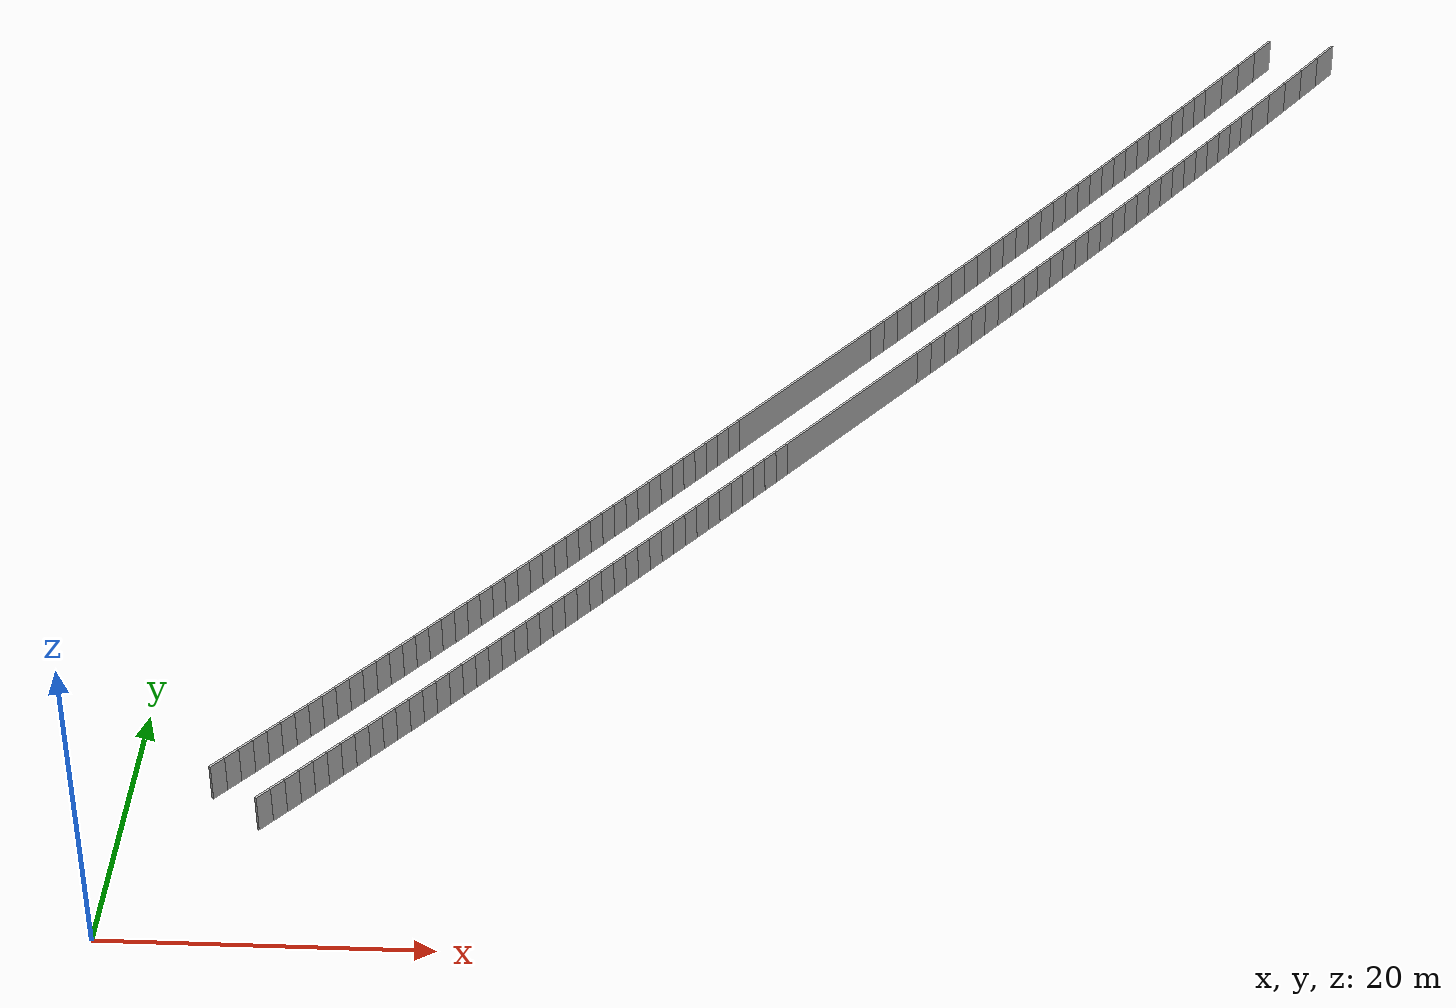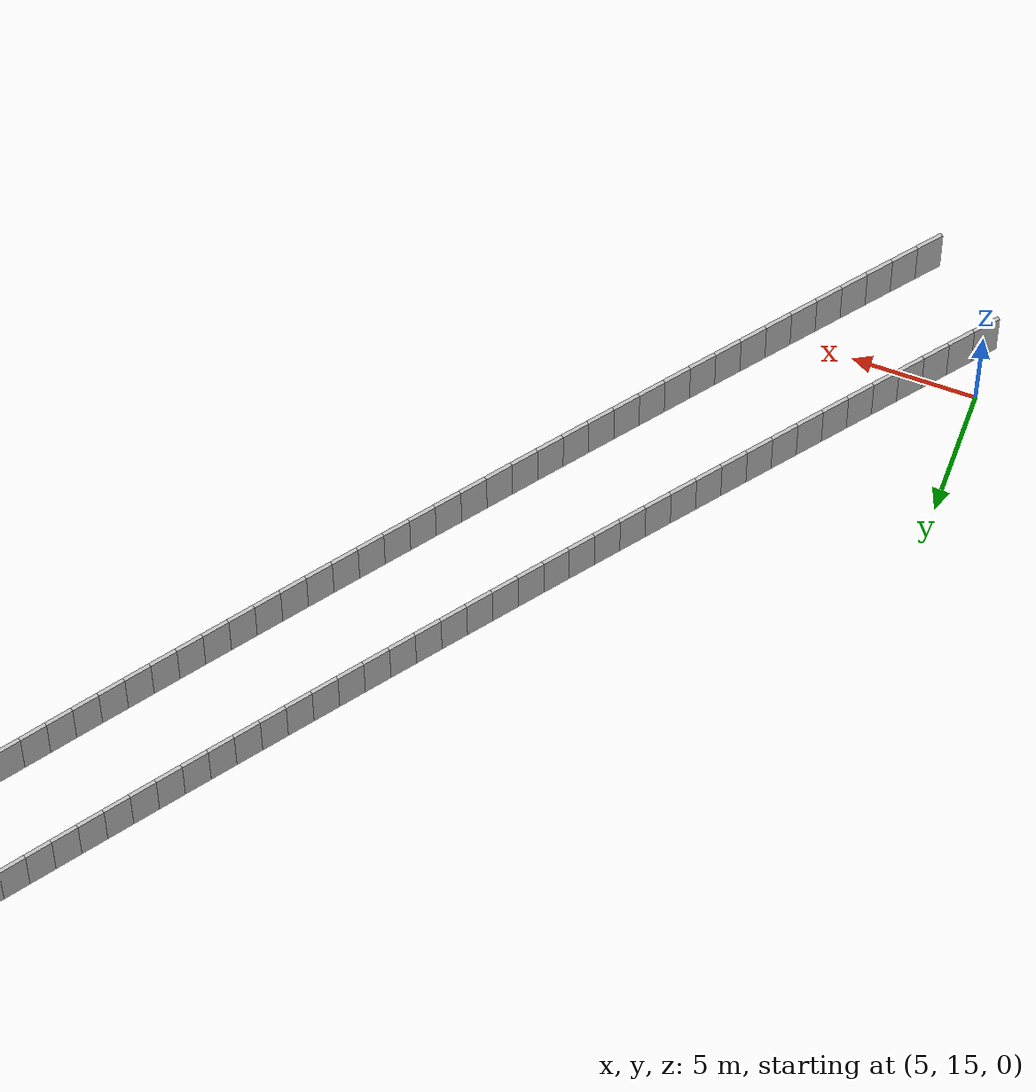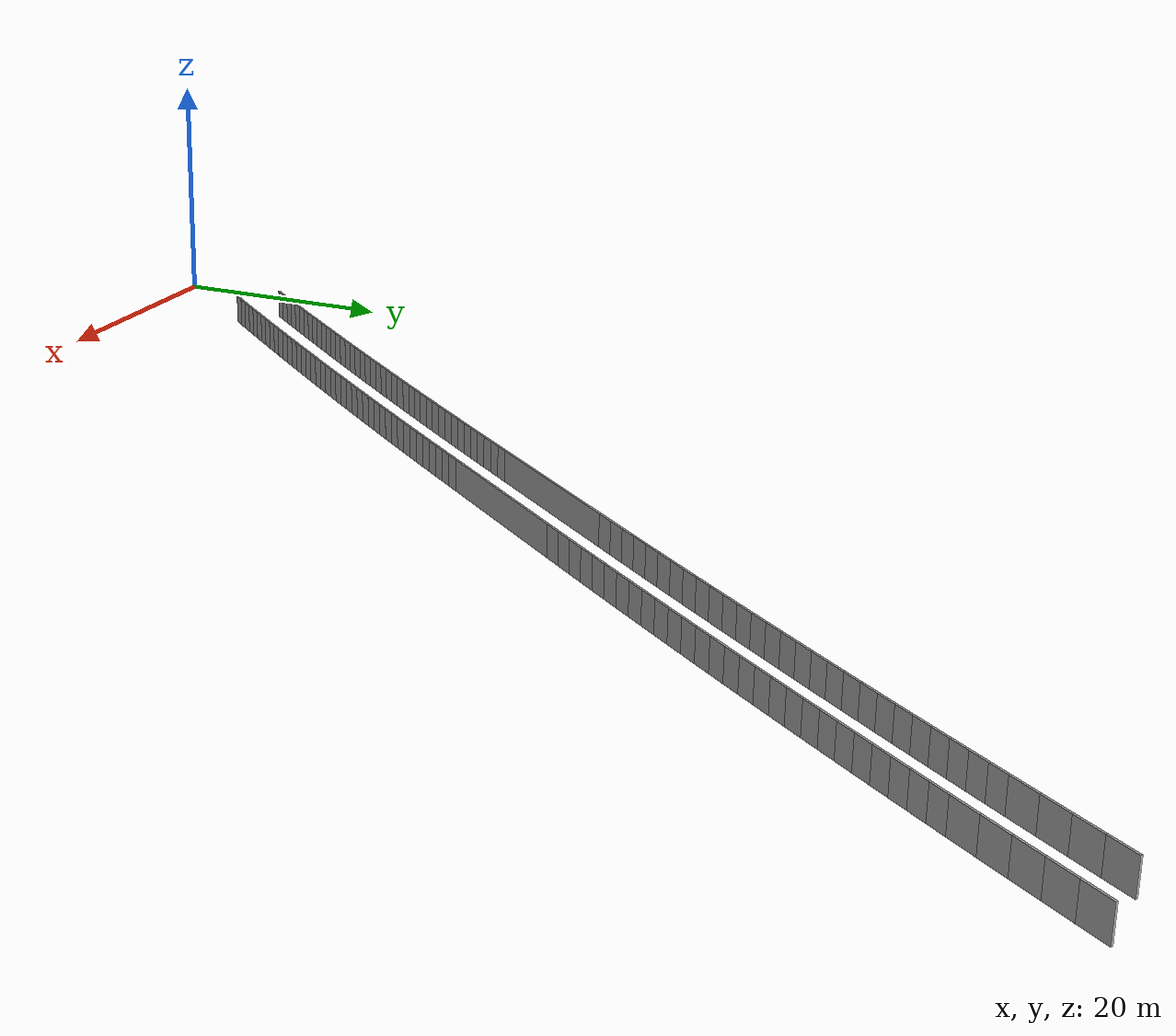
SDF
<?xml version="1.0" ?>
<sdf version="1.6">
  <model name="sps_2106">
    <pose frame="">0 0 0 0 -0 0</pose>
    <static>1</static>
    <self_collide>0</self_collide>
    <allow_auto_disable>0</allow_auto_disable>
    <link name="Wall250">
      <kinematic>0</kinematic>
      <gravity>1</gravity>
      <self_collide>0</self_collide>
      <collision name="collision">
        <geometry>
          <box>
            <size>13.7169 0.15 2.5</size>
          </box>
        </geometry>
        <pose frame="">0 0 0 0 -0 0</pose>
      </collision>
      <visual name="visual">
        <geometry>
          <box>
            <size>13.7169 0.15 2.5</size>
          </box>
        </geometry>
        <pose frame="">0 0 0 0 -0 0</pose>
        <cast_shadows>1</cast_shadows>
        <transparency>0.0</transparency>
      </visual>
      <pose frame="">41.9678 52.3142 1.25 0 0 -2.22473</pose>
    </link>
    <link name="Wall474">
      <kinematic>0</kinematic>
      <gravity>1</gravity>
      <self_collide>0</self_collide>
      <collision name="collision">
        <geometry>
          <box>
            <size>13.7281 0.15 2.5</size>
          </box>
        </geometry>
        <pose frame="">0 0 0 0 -0 0</pose>
      </collision>
      <visual name="visual">
        <geometry>
          <box>
            <size>13.7281 0.15 2.5</size>
          </box>
        </geometry>
        <pose frame="">0 0 0 0 -0 0</pose>
        <cast_shadows>1</cast_shadows>
        <transparency>0.0</transparency>
      </visual>
      <pose frame="">38.6811 54.8316 1.25 0 -0 0.916844</pose>
    </link>
    <link name="Wall4303">
      <kinematic>0</kinematic>
      <gravity>1</gravity>
      <self_collide>0</self_collide>
      <collision name="collision">
        <geometry>
          <box>
            <size>1.5025 0.15 2.5</size>
          </box>
        </geometry>
        <pose frame="">0 0 0 0 -0 0</pose>
      </collision>
      <visual name="visual">
        <geometry>
          <box>
            <size>1.5025 0.15 2.5</size>
          </box>
        </geometry>
        <pose frame="">0 0 0 0 -0 0</pose>
        <cast_shadows>1</cast_shadows>
        <transparency>0.0</transparency>
      </visual>
      <pose frame="">46.5969 58.3539 1.25 0 -0 0.916701</pose>
    </link>
    <link name="Wall4304">
      <kinematic>0</kinematic>
      <gravity>1</gravity>
      <self_collide>0</self_collide>
      <collision name="collision">
        <geometry>
          <box>
            <size>1.50299 0.15 2.5</size>
          </box>
        </geometry>
        <pose frame="">0 0 0 0 -0 0</pose>
      </collision>
      <visual name="visual">
        <geometry>
          <box>
            <size>1.50299 0.15 2.5</size>
          </box>
        </geometry>
        <pose frame="">0 0 0 0 -0 0</pose>
        <cast_shadows>1</cast_shadows>
        <transparency>0.0</transparency>
      </visual>
      <pose frame="">47.5103 59.5472 1.25 0 -0 0.91828</pose>
    </link>
    <link name="Wall4305">
      <kinematic>0</kinematic>
      <gravity>1</gravity>
      <self_collide>0</self_collide>
      <collision name="collision">
        <geometry>
          <box>
            <size>1.50314 0.15 2.5</size>
          </box>
        </geometry>
        <pose frame="">0 0 0 0 -0 0</pose>
      </collision>
      <visual name="visual">
        <geometry>
          <box>
            <size>1.50314 0.15 2.5</size>
          </box>
        </geometry>
        <pose frame="">0 0 0 0 -0 0</pose>
        <cast_shadows>1</cast_shadows>
        <transparency>0.0</transparency>
      </visual>
      <pose frame="">48.4221 60.7421 1.25 0 -0 0.919686</pose>
    </link>
    <link name="Wall4306">
      <kinematic>0</kinematic>
      <gravity>1</gravity>
      <self_collide>0</self_collide>
      <collision name="collision">
        <geometry>
          <box>
            <size>1.50288 0.15 2.5</size>
          </box>
        </geometry>
        <pose frame="">0 0 0 0 -0 0</pose>
      </collision>
      <visual name="visual">
        <geometry>
          <box>
            <size>1.50288 0.15 2.5</size>
          </box>
        </geometry>
        <pose frame="">0 0 0 0 -0 0</pose>
        <cast_shadows>1</cast_shadows>
        <transparency>0.0</transparency>
      </visual>
      <pose frame="">49.3321 61.9384 1.25 0 -0 0.92139</pose>
    </link>
    <link name="Wall4307">
      <kinematic>0</kinematic>
      <gravity>1</gravity>
      <self_collide>0</self_collide>
      <collision name="collision">
        <geometry>
          <box>
            <size>1.50309 0.15 2.5</size>
          </box>
        </geometry>
        <pose frame="">0 0 0 0 -0 0</pose>
      </collision>
      <visual name="visual">
        <geometry>
          <box>
            <size>1.50309 0.15 2.5</size>
          </box>
        </geometry>
        <pose frame="">0 0 0 0 -0 0</pose>
        <cast_shadows>1</cast_shadows>
        <transparency>0.0</transparency>
      </visual>
      <pose frame="">50.24 63.1362 1.25 0 -0 0.923023</pose>
    </link>
    <link name="Wall4308">
      <kinematic>0</kinematic>
      <gravity>1</gravity>
      <self_collide>0</self_collide>
      <collision name="collision">
        <geometry>
          <box>
            <size>1.50314 0.15 2.5</size>
          </box>
        </geometry>
        <pose frame="">0 0 0 0 -0 0</pose>
      </collision>
      <visual name="visual">
        <geometry>
          <box>
            <size>1.50314 0.15 2.5</size>
          </box>
        </geometry>
        <pose frame="">0 0 0 0 -0 0</pose>
        <cast_shadows>1</cast_shadows>
        <transparency>0.0</transparency>
      </visual>
      <pose frame="">51.146 64.3355 1.25 0 -0 0.924526</pose>
    </link>
    <link name="Wall4309">
      <kinematic>0</kinematic>
      <gravity>1</gravity>
      <self_collide>0</self_collide>
      <collision name="collision">
        <geometry>
          <box>
            <size>1.50305 0.15 2.5</size>
          </box>
        </geometry>
        <pose frame="">0 0 0 0 -0 0</pose>
      </collision>
      <visual name="visual">
        <geometry>
          <box>
            <size>1.50305 0.15 2.5</size>
          </box>
        </geometry>
        <pose frame="">0 0 0 0 -0 0</pose>
        <cast_shadows>1</cast_shadows>
        <transparency>0.0</transparency>
      </visual>
      <pose frame="">52.0503 65.5362 1.25 0 -0 0.926158</pose>
    </link>
    <link name="Wall4310">
      <kinematic>0</kinematic>
      <gravity>1</gravity>
      <self_collide>0</self_collide>
      <collision name="collision">
        <geometry>
          <box>
            <size>1.50306 0.15 2.5</size>
          </box>
        </geometry>
        <pose frame="">0 0 0 0 -0 0</pose>
      </collision>
      <visual name="visual">
        <geometry>
          <box>
            <size>1.50306 0.15 2.5</size>
          </box>
        </geometry>
        <pose frame="">0 0 0 0 -0 0</pose>
        <cast_shadows>1</cast_shadows>
        <transparency>0.0</transparency>
      </visual>
      <pose frame="">52.9526 66.7383 1.25 0 -0 0.927636</pose>
    </link>
    <link name="Wall4311">
      <kinematic>0</kinematic>
      <gravity>1</gravity>
      <self_collide>0</self_collide>
      <collision name="collision">
        <geometry>
          <box>
            <size>1.50314 0.15 2.5</size>
          </box>
        </geometry>
        <pose frame="">0 0 0 0 -0 0</pose>
      </collision>
      <visual name="visual">
        <geometry>
          <box>
            <size>1.50314 0.15 2.5</size>
          </box>
        </geometry>
        <pose frame="">0 0 0 0 -0 0</pose>
        <cast_shadows>1</cast_shadows>
        <transparency>0.0</transparency>
      </visual>
      <pose frame="">53.853 67.9419 1.25 0 -0 0.929399</pose>
    </link>
    <link name="Wall4312">
      <kinematic>0</kinematic>
      <gravity>1</gravity>
      <self_collide>0</self_collide>
      <collision name="collision">
        <geometry>
          <box>
            <size>1.5031 0.15 2.5</size>
          </box>
        </geometry>
        <pose frame="">0 0 0 0 -0 0</pose>
      </collision>
      <visual name="visual">
        <geometry>
          <box>
            <size>1.5031 0.15 2.5</size>
          </box>
        </geometry>
        <pose frame="">0 0 0 0 -0 0</pose>
        <cast_shadows>1</cast_shadows>
        <transparency>0.0</transparency>
      </visual>
      <pose frame="">54.7515 69.1469 1.25 0 -0 0.930795</pose>
    </link>
    <link name="Wall4313">
      <kinematic>0</kinematic>
      <gravity>1</gravity>
      <self_collide>0</self_collide>
      <collision name="collision">
        <geometry>
          <box>
            <size>1.50308 0.15 2.5</size>
          </box>
        </geometry>
        <pose frame="">0 0 0 0 -0 0</pose>
      </collision>
      <visual name="visual">
        <geometry>
          <box>
            <size>1.50308 0.15 2.5</size>
          </box>
        </geometry>
        <pose frame="">0 0 0 0 -0 0</pose>
        <cast_shadows>1</cast_shadows>
        <transparency>0.0</transparency>
      </visual>
      <pose frame="">55.6481 70.3533 1.25 0 -0 0.932509</pose>
    </link>
    <link name="Wall4314">
      <kinematic>0</kinematic>
      <gravity>1</gravity>
      <self_collide>0</self_collide>
      <collision name="collision">
        <geometry>
          <box>
            <size>1.5031 0.15 2.5</size>
          </box>
        </geometry>
        <pose frame="">0 0 0 0 -0 0</pose>
      </collision>
      <visual name="visual">
        <geometry>
          <box>
            <size>1.5031 0.15 2.5</size>
          </box>
        </geometry>
        <pose frame="">0 0 0 0 -0 0</pose>
        <cast_shadows>1</cast_shadows>
        <transparency>0.0</transparency>
      </visual>
      <pose frame="">56.5427 71.5612 1.25 0 -0 0.934133</pose>
    </link>
    <link name="Wall4315">
      <kinematic>0</kinematic>
      <gravity>1</gravity>
      <self_collide>0</self_collide>
      <collision name="collision">
        <geometry>
          <box>
            <size>1.50325 0.15 2.5</size>
          </box>
        </geometry>
        <pose frame="">0 0 0 0 -0 0</pose>
      </collision>
      <visual name="visual">
        <geometry>
          <box>
            <size>1.50325 0.15 2.5</size>
          </box>
        </geometry>
        <pose frame="">0 0 0 0 -0 0</pose>
        <cast_shadows>1</cast_shadows>
        <transparency>0.0</transparency>
      </visual>
      <pose frame="">57.4354 72.7705 1.25 0 -0 0.93557</pose>
    </link>
    <link name="Wall4316">
      <kinematic>0</kinematic>
      <gravity>1</gravity>
      <self_collide>0</self_collide>
      <collision name="collision">
        <geometry>
          <box>
            <size>1.50292 0.15 2.5</size>
          </box>
        </geometry>
        <pose frame="">0 0 0 0 -0 0</pose>
      </collision>
      <visual name="visual">
        <geometry>
          <box>
            <size>1.50292 0.15 2.5</size>
          </box>
        </geometry>
        <pose frame="">0 0 0 0 -0 0</pose>
        <cast_shadows>1</cast_shadows>
        <transparency>0.0</transparency>
      </visual>
      <pose frame="">58.3263 73.9811 1.25 0 -0 0.937172</pose>
    </link>
    <link name="Wall4317">
      <kinematic>0</kinematic>
      <gravity>1</gravity>
      <self_collide>0</self_collide>
      <collision name="collision">
        <geometry>
          <box>
            <size>1.50368 0.15 2.5</size>
          </box>
        </geometry>
        <pose frame="">0 0 0 0 -0 0</pose>
      </collision>
      <visual name="visual">
        <geometry>
          <box>
            <size>1.50368 0.15 2.5</size>
          </box>
        </geometry>
        <pose frame="">0 0 0 0 -0 0</pose>
        <cast_shadows>1</cast_shadows>
        <transparency>0.0</transparency>
      </visual>
      <pose frame="">59.2154 75.1933 1.25 0 -0 0.93875</pose>
    </link>
    <link name="Wall4318">
      <kinematic>0</kinematic>
      <gravity>1</gravity>
      <self_collide>0</self_collide>
      <collision name="collision">
        <geometry>
          <box>
            <size>1.50314 0.15 2.5</size>
          </box>
        </geometry>
        <pose frame="">0 0 0 0 -0 0</pose>
      </collision>
      <visual name="visual">
        <geometry>
          <box>
            <size>1.50314 0.15 2.5</size>
          </box>
        </geometry>
        <pose frame="">0 0 0 0 -0 0</pose>
        <cast_shadows>1</cast_shadows>
        <transparency>0.0</transparency>
      </visual>
      <pose frame="">60.1027 76.407 1.25 0 -0 0.940403</pose>
    </link>
    <link name="Wall4319">
      <kinematic>0</kinematic>
      <gravity>1</gravity>
      <self_collide>0</self_collide>
      <collision name="collision">
        <geometry>
          <box>
            <size>1.50312 0.15 2.5</size>
          </box>
        </geometry>
        <pose frame="">0 0 0 0 -0 0</pose>
      </collision>
      <visual name="visual">
        <geometry>
          <box>
            <size>1.50312 0.15 2.5</size>
          </box>
        </geometry>
        <pose frame="">0 0 0 0 -0 0</pose>
        <cast_shadows>1</cast_shadows>
        <transparency>0.0</transparency>
      </visual>
      <pose frame="">60.9878 77.6219 1.25 0 -0 0.941946</pose>
    </link>
    <link name="Wall4320">
      <kinematic>0</kinematic>
      <gravity>1</gravity>
      <self_collide>0</self_collide>
      <collision name="collision">
        <geometry>
          <box>
            <size>1.5031 0.15 2.5</size>
          </box>
        </geometry>
        <pose frame="">0 0 0 0 -0 0</pose>
      </collision>
      <visual name="visual">
        <geometry>
          <box>
            <size>1.5031 0.15 2.5</size>
          </box>
        </geometry>
        <pose frame="">0 0 0 0 -0 0</pose>
        <cast_shadows>1</cast_shadows>
        <transparency>0.0</transparency>
      </visual>
      <pose frame="">61.8709 78.8382 1.25 0 -0 0.943546</pose>
    </link>
    <link name="Wall4321">
      <kinematic>0</kinematic>
      <gravity>1</gravity>
      <self_collide>0</self_collide>
      <collision name="collision">
        <geometry>
          <box>
            <size>1.50315 0.15 2.5</size>
          </box>
        </geometry>
        <pose frame="">0 0 0 0 -0 0</pose>
      </collision>
      <visual name="visual">
        <geometry>
          <box>
            <size>1.50315 0.15 2.5</size>
          </box>
        </geometry>
        <pose frame="">0 0 0 0 -0 0</pose>
        <cast_shadows>1</cast_shadows>
        <transparency>0.0</transparency>
      </visual>
      <pose frame="">62.7522 80.0559 1.25 0 -0 0.94517</pose>
    </link>
    <link name="Wall4322">
      <kinematic>0</kinematic>
      <gravity>1</gravity>
      <self_collide>0</self_collide>
      <collision name="collision">
        <geometry>
          <box>
            <size>1.50302 0.15 2.5</size>
          </box>
        </geometry>
        <pose frame="">0 0 0 0 -0 0</pose>
      </collision>
      <visual name="visual">
        <geometry>
          <box>
            <size>1.50302 0.15 2.5</size>
          </box>
        </geometry>
        <pose frame="">0 0 0 0 -0 0</pose>
        <cast_shadows>1</cast_shadows>
        <transparency>0.0</transparency>
      </visual>
      <pose frame="">63.6314 81.275 1.25 0 -0 0.946813</pose>
    </link>
    <link name="Wall4323">
      <kinematic>0</kinematic>
      <gravity>1</gravity>
      <self_collide>0</self_collide>
      <collision name="collision">
        <geometry>
          <box>
            <size>1.50313 0.15 2.5</size>
          </box>
        </geometry>
        <pose frame="">0 0 0 0 -0 0</pose>
      </collision>
      <visual name="visual">
        <geometry>
          <box>
            <size>1.50313 0.15 2.5</size>
          </box>
        </geometry>
        <pose frame="">0 0 0 0 -0 0</pose>
        <cast_shadows>1</cast_shadows>
        <transparency>0.0</transparency>
      </visual>
      <pose frame="">64.5087 82.4955 1.25 0 -0 0.948314</pose>
    </link>
    <link name="Wall4324">
      <kinematic>0</kinematic>
      <gravity>1</gravity>
      <self_collide>0</self_collide>
      <collision name="collision">
        <geometry>
          <box>
            <size>1.50295 0.15 2.5</size>
          </box>
        </geometry>
        <pose frame="">0 0 0 0 -0 0</pose>
      </collision>
      <visual name="visual">
        <geometry>
          <box>
            <size>1.50295 0.15 2.5</size>
          </box>
        </geometry>
        <pose frame="">0 0 0 0 -0 0</pose>
        <cast_shadows>1</cast_shadows>
        <transparency>0.0</transparency>
      </visual>
      <pose frame="">65.3841 83.7173 1.25 0 -0 0.949876</pose>
    </link>
    <link name="Wall4325">
      <kinematic>0</kinematic>
      <gravity>1</gravity>
      <self_collide>0</self_collide>
      <collision name="collision">
        <geometry>
          <box>
            <size>1.50307 0.15 2.5</size>
          </box>
        </geometry>
        <pose frame="">0 0 0 0 -0 0</pose>
      </collision>
      <visual name="visual">
        <geometry>
          <box>
            <size>1.50307 0.15 2.5</size>
          </box>
        </geometry>
        <pose frame="">0 0 0 0 -0 0</pose>
        <cast_shadows>1</cast_shadows>
        <transparency>0.0</transparency>
      </visual>
      <pose frame="">66.2574 84.9405 1.25 0 -0 0.951581</pose>
    </link>
    <link name="Wall4326">
      <kinematic>0</kinematic>
      <gravity>1</gravity>
      <self_collide>0</self_collide>
      <collision name="collision">
        <geometry>
          <box>
            <size>1.50299 0.15 2.5</size>
          </box>
        </geometry>
        <pose frame="">0 0 0 0 -0 0</pose>
      </collision>
      <visual name="visual">
        <geometry>
          <box>
            <size>1.50299 0.15 2.5</size>
          </box>
        </geometry>
        <pose frame="">0 0 0 0 -0 0</pose>
        <cast_shadows>1</cast_shadows>
        <transparency>0.0</transparency>
      </visual>
      <pose frame="">67.1289 86.1651 1.25 0 -0 0.952987</pose>
    </link>
    <link name="Wall4327">
      <kinematic>0</kinematic>
      <gravity>1</gravity>
      <self_collide>0</self_collide>
      <collision name="collision">
        <geometry>
          <box>
            <size>1.5032 0.15 2.5</size>
          </box>
        </geometry>
        <pose frame="">0 0 0 0 -0 0</pose>
      </collision>
      <visual name="visual">
        <geometry>
          <box>
            <size>1.5032 0.15 2.5</size>
          </box>
        </geometry>
        <pose frame="">0 0 0 0 -0 0</pose>
        <cast_shadows>1</cast_shadows>
        <transparency>0.0</transparency>
      </visual>
      <pose frame="">67.9986 87.3911 1.25 0 -0 0.954682</pose>
    </link>
    <link name="Wall4328">
      <kinematic>0</kinematic>
      <gravity>1</gravity>
      <self_collide>0</self_collide>
      <collision name="collision">
        <geometry>
          <box>
            <size>1.50325 0.15 2.5</size>
          </box>
        </geometry>
        <pose frame="">0 0 0 0 -0 0</pose>
      </collision>
      <visual name="visual">
        <geometry>
          <box>
            <size>1.50325 0.15 2.5</size>
          </box>
        </geometry>
        <pose frame="">0 0 0 0 -0 0</pose>
        <cast_shadows>1</cast_shadows>
        <transparency>0.0</transparency>
      </visual>
      <pose frame="">68.8663 88.6186 1.25 0 -0 0.956248</pose>
    </link>
    <link name="Wall4329">
      <kinematic>0</kinematic>
      <gravity>1</gravity>
      <self_collide>0</self_collide>
      <collision name="collision">
        <geometry>
          <box>
            <size>1.50313 0.15 2.5</size>
          </box>
        </geometry>
        <pose frame="">0 0 0 0 -0 0</pose>
      </collision>
      <visual name="visual">
        <geometry>
          <box>
            <size>1.50313 0.15 2.5</size>
          </box>
        </geometry>
        <pose frame="">0 0 0 0 -0 0</pose>
        <cast_shadows>1</cast_shadows>
        <transparency>0.0</transparency>
      </visual>
      <pose frame="">69.732 89.8474 1.25 0 -0 0.957778</pose>
    </link>
    <link name="Wall4330">
      <kinematic>0</kinematic>
      <gravity>1</gravity>
      <self_collide>0</self_collide>
      <collision name="collision">
        <geometry>
          <box>
            <size>2.25437 0.15 2.5</size>
          </box>
        </geometry>
        <pose frame="">0 0 0 0 -0 0</pose>
      </collision>
      <visual name="visual">
        <geometry>
          <box>
            <size>2.25437 0.15 2.5</size>
          </box>
        </geometry>
        <pose frame="">0 0 0 0 -0 0</pose>
        <cast_shadows>1</cast_shadows>
        <transparency>0.0</transparency>
      </visual>
      <pose frame="">70.8111 91.3854 1.25 0 -0 0.959844</pose>
    </link>
    <link name="Wall4331">
      <kinematic>0</kinematic>
      <gravity>1</gravity>
      <self_collide>0</self_collide>
      <collision name="collision">
        <geometry>
          <box>
            <size>2.25446 0.15 2.5</size>
          </box>
        </geometry>
        <pose frame="">0 0 0 0 -0 0</pose>
      </collision>
      <visual name="visual">
        <geometry>
          <box>
            <size>2.25446 0.15 2.5</size>
          </box>
        </geometry>
        <pose frame="">0 0 0 0 -0 0</pose>
        <cast_shadows>1</cast_shadows>
        <transparency>0.0</transparency>
      </visual>
      <pose frame="">72.1022 93.2335 1.25 0 -0 0.962151</pose>
    </link>
    <link name="Wall4332">
      <kinematic>0</kinematic>
      <gravity>1</gravity>
      <self_collide>0</self_collide>
      <collision name="collision">
        <geometry>
          <box>
            <size>2.25441 0.15 2.5</size>
          </box>
        </geometry>
        <pose frame="">0 0 0 0 -0 0</pose>
      </collision>
      <visual name="visual">
        <geometry>
          <box>
            <size>2.25441 0.15 2.5</size>
          </box>
        </geometry>
        <pose frame="">0 0 0 0 -0 0</pose>
        <cast_shadows>1</cast_shadows>
        <transparency>0.0</transparency>
      </visual>
      <pose frame="">73.389 95.0846 1.25 0 -0 0.964509</pose>
    </link>
    <link name="Wall4333">
      <kinematic>0</kinematic>
      <gravity>1</gravity>
      <self_collide>0</self_collide>
      <collision name="collision">
        <geometry>
          <box>
            <size>2.25487 0.15 2.5</size>
          </box>
        </geometry>
        <pose frame="">0 0 0 0 -0 0</pose>
      </collision>
      <visual name="visual">
        <geometry>
          <box>
            <size>2.25487 0.15 2.5</size>
          </box>
        </geometry>
        <pose frame="">0 0 0 0 -0 0</pose>
        <cast_shadows>1</cast_shadows>
        <transparency>0.0</transparency>
      </visual>
      <pose frame="">74.6714 96.939 1.25 0 -0 0.96702</pose>
    </link>
    <link name="Wall4334">
      <kinematic>0</kinematic>
      <gravity>1</gravity>
      <self_collide>0</self_collide>
      <collision name="collision">
        <geometry>
          <box>
            <size>2.25466 0.15 2.5</size>
          </box>
        </geometry>
        <pose frame="">0 0 0 0 -0 0</pose>
      </collision>
      <visual name="visual">
        <geometry>
          <box>
            <size>2.25466 0.15 2.5</size>
          </box>
        </geometry>
        <pose frame="">0 0 0 0 -0 0</pose>
        <cast_shadows>1</cast_shadows>
        <transparency>0.0</transparency>
      </visual>
      <pose frame="">75.9494 98.7966 1.25 0 -0 0.969354</pose>
    </link>
    <link name="Wall6028">
      <kinematic>0</kinematic>
      <gravity>1</gravity>
      <self_collide>0</self_collide>
      <collision name="collision">
        <geometry>
          <box>
            <size>1.49649 0.15 2.5</size>
          </box>
        </geometry>
        <pose frame="">0 0 0 0 -0 0</pose>
      </collision>
      <visual name="visual">
        <geometry>
          <box>
            <size>1.49649 0.15 2.5</size>
          </box>
        </geometry>
        <pose frame="">0 0 0 0 -0 0</pose>
        <cast_shadows>1</cast_shadows>
        <transparency>0.0</transparency>
      </visual>
      <pose frame="">43.3121 60.8732 1.25 0 -0 0.916446</pose>
    </link>
    <link name="Wall6029">
      <kinematic>0</kinematic>
      <gravity>1</gravity>
      <self_collide>0</self_collide>
      <collision name="collision">
        <geometry>
          <box>
            <size>1.49653 0.15 2.5</size>
          </box>
        </geometry>
        <pose frame="">0 0 0 0 -0 0</pose>
      </collision>
      <visual name="visual">
        <geometry>
          <box>
            <size>1.49653 0.15 2.5</size>
          </box>
        </geometry>
        <pose frame="">0 0 0 0 -0 0</pose>
        <cast_shadows>1</cast_shadows>
        <transparency>0.0</transparency>
      </visual>
      <pose frame="">44.2219 62.0614 1.25 0 -0 0.918216</pose>
    </link>
    <link name="Wall6030">
      <kinematic>0</kinematic>
      <gravity>1</gravity>
      <self_collide>0</self_collide>
      <collision name="collision">
        <geometry>
          <box>
            <size>1.49642 0.15 2.5</size>
          </box>
        </geometry>
        <pose frame="">0 0 0 0 -0 0</pose>
      </collision>
      <visual name="visual">
        <geometry>
          <box>
            <size>1.49642 0.15 2.5</size>
          </box>
        </geometry>
        <pose frame="">0 0 0 0 -0 0</pose>
        <cast_shadows>1</cast_shadows>
        <transparency>0.0</transparency>
      </visual>
      <pose frame="">45.1296 63.2511 1.25 0 -0 0.919798</pose>
    </link>
    <link name="Wall6031">
      <kinematic>0</kinematic>
      <gravity>1</gravity>
      <self_collide>0</self_collide>
      <collision name="collision">
        <geometry>
          <box>
            <size>1.49662 0.15 2.5</size>
          </box>
        </geometry>
        <pose frame="">0 0 0 0 -0 0</pose>
      </collision>
      <visual name="visual">
        <geometry>
          <box>
            <size>1.49662 0.15 2.5</size>
          </box>
        </geometry>
        <pose frame="">0 0 0 0 -0 0</pose>
        <cast_shadows>1</cast_shadows>
        <transparency>0.0</transparency>
      </visual>
      <pose frame="">46.0356 64.4422 1.25 0 -0 0.921235</pose>
    </link>
    <link name="Wall6032">
      <kinematic>0</kinematic>
      <gravity>1</gravity>
      <self_collide>0</self_collide>
      <collision name="collision">
        <geometry>
          <box>
            <size>1.49636 0.15 2.5</size>
          </box>
        </geometry>
        <pose frame="">0 0 0 0 -0 0</pose>
      </collision>
      <visual name="visual">
        <geometry>
          <box>
            <size>1.49636 0.15 2.5</size>
          </box>
        </geometry>
        <pose frame="">0 0 0 0 -0 0</pose>
        <cast_shadows>1</cast_shadows>
        <transparency>0.0</transparency>
      </visual>
      <pose frame="">46.9398 65.6347 1.25 0 -0 0.922947</pose>
    </link>
    <link name="Wall6033">
      <kinematic>0</kinematic>
      <gravity>1</gravity>
      <self_collide>0</self_collide>
      <collision name="collision">
        <geometry>
          <box>
            <size>1.49658 0.15 2.5</size>
          </box>
        </geometry>
        <pose frame="">0 0 0 0 -0 0</pose>
      </collision>
      <visual name="visual">
        <geometry>
          <box>
            <size>1.49658 0.15 2.5</size>
          </box>
        </geometry>
        <pose frame="">0 0 0 0 -0 0</pose>
        <cast_shadows>1</cast_shadows>
        <transparency>0.0</transparency>
      </visual>
      <pose frame="">47.8418 66.8287 1.25 0 -0 0.924587</pose>
    </link>
    <link name="Wall6034">
      <kinematic>0</kinematic>
      <gravity>1</gravity>
      <self_collide>0</self_collide>
      <collision name="collision">
        <geometry>
          <box>
            <size>1.49658 0.15 2.5</size>
          </box>
        </geometry>
        <pose frame="">0 0 0 0 -0 0</pose>
      </collision>
      <visual name="visual">
        <geometry>
          <box>
            <size>1.49658 0.15 2.5</size>
          </box>
        </geometry>
        <pose frame="">0 0 0 0 -0 0</pose>
        <cast_shadows>1</cast_shadows>
        <transparency>0.0</transparency>
      </visual>
      <pose frame="">48.7421 68.0242 1.25 0 -0 0.926072</pose>
    </link>
    <link name="Wall6035">
      <kinematic>0</kinematic>
      <gravity>1</gravity>
      <self_collide>0</self_collide>
      <collision name="collision">
        <geometry>
          <box>
            <size>1.49655 0.15 2.5</size>
          </box>
        </geometry>
        <pose frame="">0 0 0 0 -0 0</pose>
      </collision>
      <visual name="visual">
        <geometry>
          <box>
            <size>1.49655 0.15 2.5</size>
          </box>
        </geometry>
        <pose frame="">0 0 0 0 -0 0</pose>
        <cast_shadows>1</cast_shadows>
        <transparency>0.0</transparency>
      </visual>
      <pose frame="">49.6406 69.2211 1.25 0 -0 0.927736</pose>
    </link>
    <link name="Wall6036">
      <kinematic>0</kinematic>
      <gravity>1</gravity>
      <self_collide>0</self_collide>
      <collision name="collision">
        <geometry>
          <box>
            <size>1.49641 0.15 2.5</size>
          </box>
        </geometry>
        <pose frame="">0 0 0 0 -0 0</pose>
      </collision>
      <visual name="visual">
        <geometry>
          <box>
            <size>1.49641 0.15 2.5</size>
          </box>
        </geometry>
        <pose frame="">0 0 0 0 -0 0</pose>
        <cast_shadows>1</cast_shadows>
        <transparency>0.0</transparency>
      </visual>
      <pose frame="">50.5369 70.4194 1.25 0 -0 0.929351</pose>
    </link>
    <link name="Wall6037">
      <kinematic>0</kinematic>
      <gravity>1</gravity>
      <self_collide>0</self_collide>
      <collision name="collision">
        <geometry>
          <box>
            <size>1.49653 0.15 2.5</size>
          </box>
        </geometry>
        <pose frame="">0 0 0 0 -0 0</pose>
      </collision>
      <visual name="visual">
        <geometry>
          <box>
            <size>1.49653 0.15 2.5</size>
          </box>
        </geometry>
        <pose frame="">0 0 0 0 -0 0</pose>
        <cast_shadows>1</cast_shadows>
        <transparency>0.0</transparency>
      </visual>
      <pose frame="">51.4314 71.6191 1.25 0 -0 0.930884</pose>
    </link>
    <link name="Wall6038">
      <kinematic>0</kinematic>
      <gravity>1</gravity>
      <self_collide>0</self_collide>
      <collision name="collision">
        <geometry>
          <box>
            <size>1.49655 0.15 2.5</size>
          </box>
        </geometry>
        <pose frame="">0 0 0 0 -0 0</pose>
      </collision>
      <visual name="visual">
        <geometry>
          <box>
            <size>1.49655 0.15 2.5</size>
          </box>
        </geometry>
        <pose frame="">0 0 0 0 -0 0</pose>
        <cast_shadows>1</cast_shadows>
        <transparency>0.0</transparency>
      </visual>
      <pose frame="">52.3241 72.8203 1.25 0 -0 0.932573</pose>
    </link>
    <link name="Wall6039">
      <kinematic>0</kinematic>
      <gravity>1</gravity>
      <self_collide>0</self_collide>
      <collision name="collision">
        <geometry>
          <box>
            <size>1.49645 0.15 2.5</size>
          </box>
        </geometry>
        <pose frame="">0 0 0 0 -0 0</pose>
      </collision>
      <visual name="visual">
        <geometry>
          <box>
            <size>1.49645 0.15 2.5</size>
          </box>
        </geometry>
        <pose frame="">0 0 0 0 -0 0</pose>
        <cast_shadows>1</cast_shadows>
        <transparency>0.0</transparency>
      </visual>
      <pose frame="">53.2147 74.0229 1.25 0 -0 0.934041</pose>
    </link>
    <link name="Wall6040">
      <kinematic>0</kinematic>
      <gravity>1</gravity>
      <self_collide>0</self_collide>
      <collision name="collision">
        <geometry>
          <box>
            <size>1.49657 0.15 2.5</size>
          </box>
        </geometry>
        <pose frame="">0 0 0 0 -0 0</pose>
      </collision>
      <visual name="visual">
        <geometry>
          <box>
            <size>1.49657 0.15 2.5</size>
          </box>
        </geometry>
        <pose frame="">0 0 0 0 -0 0</pose>
        <cast_shadows>1</cast_shadows>
        <transparency>0.0</transparency>
      </visual>
      <pose frame="">54.1036 75.2268 1.25 0 -0 0.935574</pose>
    </link>
    <link name="Wall6041">
      <kinematic>0</kinematic>
      <gravity>1</gravity>
      <self_collide>0</self_collide>
      <collision name="collision">
        <geometry>
          <box>
            <size>1.4965 0.15 2.5</size>
          </box>
        </geometry>
        <pose frame="">0 0 0 0 -0 0</pose>
      </collision>
      <visual name="visual">
        <geometry>
          <box>
            <size>1.4965 0.15 2.5</size>
          </box>
        </geometry>
        <pose frame="">0 0 0 0 -0 0</pose>
        <cast_shadows>1</cast_shadows>
        <transparency>0.0</transparency>
      </visual>
      <pose frame="">54.9907 76.4321 1.25 0 -0 0.937157</pose>
    </link>
    <link name="Wall6042">
      <kinematic>0</kinematic>
      <gravity>1</gravity>
      <self_collide>0</self_collide>
      <collision name="collision">
        <geometry>
          <box>
            <size>1.49666 0.15 2.5</size>
          </box>
        </geometry>
        <pose frame="">0 0 0 0 -0 0</pose>
      </collision>
      <visual name="visual">
        <geometry>
          <box>
            <size>1.49666 0.15 2.5</size>
          </box>
        </geometry>
        <pose frame="">0 0 0 0 -0 0</pose>
        <cast_shadows>1</cast_shadows>
        <transparency>0.0</transparency>
      </visual>
      <pose frame="">55.8758 77.6389 1.25 0 -0 0.938804</pose>
    </link>
    <link name="Wall6043">
      <kinematic>0</kinematic>
      <gravity>1</gravity>
      <self_collide>0</self_collide>
      <collision name="collision">
        <geometry>
          <box>
            <size>1.49638 0.15 2.5</size>
          </box>
        </geometry>
        <pose frame="">0 0 0 0 -0 0</pose>
      </collision>
      <visual name="visual">
        <geometry>
          <box>
            <size>1.49638 0.15 2.5</size>
          </box>
        </geometry>
        <pose frame="">0 0 0 0 -0 0</pose>
        <cast_shadows>1</cast_shadows>
        <transparency>0.0</transparency>
      </visual>
      <pose frame="">56.7588 78.8471 1.25 0 -0 0.940438</pose>
    </link>
    <link name="Wall6044">
      <kinematic>0</kinematic>
      <gravity>1</gravity>
      <self_collide>0</self_collide>
      <collision name="collision">
        <geometry>
          <box>
            <size>1.49659 0.15 2.5</size>
          </box>
        </geometry>
        <pose frame="">0 0 0 0 -0 0</pose>
      </collision>
      <visual name="visual">
        <geometry>
          <box>
            <size>1.49659 0.15 2.5</size>
          </box>
        </geometry>
        <pose frame="">0 0 0 0 -0 0</pose>
        <cast_shadows>1</cast_shadows>
        <transparency>0.0</transparency>
      </visual>
      <pose frame="">57.6399 80.0567 1.25 0 -0 0.942051</pose>
    </link>
    <link name="Wall6045">
      <kinematic>0</kinematic>
      <gravity>1</gravity>
      <self_collide>0</self_collide>
      <collision name="collision">
        <geometry>
          <box>
            <size>1.49668 0.15 2.5</size>
          </box>
        </geometry>
        <pose frame="">0 0 0 0 -0 0</pose>
      </collision>
      <visual name="visual">
        <geometry>
          <box>
            <size>1.49668 0.15 2.5</size>
          </box>
        </geometry>
        <pose frame="">0 0 0 0 -0 0</pose>
        <cast_shadows>1</cast_shadows>
        <transparency>0.0</transparency>
      </visual>
      <pose frame="">58.5192 81.2678 1.25 0 -0 0.943559</pose>
    </link>
    <link name="Wall6046">
      <kinematic>0</kinematic>
      <gravity>1</gravity>
      <self_collide>0</self_collide>
      <collision name="collision">
        <geometry>
          <box>
            <size>1.49719 0.15 2.5</size>
          </box>
        </geometry>
        <pose frame="">0 0 0 0 -0 0</pose>
      </collision>
      <visual name="visual">
        <geometry>
          <box>
            <size>1.49719 0.15 2.5</size>
          </box>
        </geometry>
        <pose frame="">0 0 0 0 -0 0</pose>
        <cast_shadows>1</cast_shadows>
        <transparency>0.0</transparency>
      </visual>
      <pose frame="">59.397 82.4804 1.25 0 -0 0.944964</pose>
    </link>
    <link name="Wall6047">
      <kinematic>0</kinematic>
      <gravity>1</gravity>
      <self_collide>0</self_collide>
      <collision name="collision">
        <geometry>
          <box>
            <size>1.4964 0.15 2.5</size>
          </box>
        </geometry>
        <pose frame="">0 0 0 0 -0 0</pose>
      </collision>
      <visual name="visual">
        <geometry>
          <box>
            <size>1.4964 0.15 2.5</size>
          </box>
        </geometry>
        <pose frame="">0 0 0 0 -0 0</pose>
        <cast_shadows>1</cast_shadows>
        <transparency>0.0</transparency>
      </visual>
      <pose frame="">60.2727 83.6943 1.25 0 -0 0.946744</pose>
    </link>
    <link name="Wall6048">
      <kinematic>0</kinematic>
      <gravity>1</gravity>
      <self_collide>0</self_collide>
      <collision name="collision">
        <geometry>
          <box>
            <size>1.49671 0.15 2.5</size>
          </box>
        </geometry>
        <pose frame="">0 0 0 0 -0 0</pose>
      </collision>
      <visual name="visual">
        <geometry>
          <box>
            <size>1.49671 0.15 2.5</size>
          </box>
        </geometry>
        <pose frame="">0 0 0 0 -0 0</pose>
        <cast_shadows>1</cast_shadows>
        <transparency>0.0</transparency>
      </visual>
      <pose frame="">61.1462 84.9095 1.25 0 -0 0.948347</pose>
    </link>
    <link name="Wall6049">
      <kinematic>0</kinematic>
      <gravity>1</gravity>
      <self_collide>0</self_collide>
      <collision name="collision">
        <geometry>
          <box>
            <size>1.49638 0.15 2.5</size>
          </box>
        </geometry>
        <pose frame="">0 0 0 0 -0 0</pose>
      </collision>
      <visual name="visual">
        <geometry>
          <box>
            <size>1.49638 0.15 2.5</size>
          </box>
        </geometry>
        <pose frame="">0 0 0 0 -0 0</pose>
        <cast_shadows>1</cast_shadows>
        <transparency>0.0</transparency>
      </visual>
      <pose frame="">62.0178 86.126 1.25 0 -0 0.949845</pose>
    </link>
    <link name="Wall6050">
      <kinematic>0</kinematic>
      <gravity>1</gravity>
      <self_collide>0</self_collide>
      <collision name="collision">
        <geometry>
          <box>
            <size>1.49645 0.15 2.5</size>
          </box>
        </geometry>
        <pose frame="">0 0 0 0 -0 0</pose>
      </collision>
      <visual name="visual">
        <geometry>
          <box>
            <size>1.49645 0.15 2.5</size>
          </box>
        </geometry>
        <pose frame="">0 0 0 0 -0 0</pose>
        <cast_shadows>1</cast_shadows>
        <transparency>0.0</transparency>
      </visual>
      <pose frame="">62.8874 87.3438 1.25 0 -0 0.951533</pose>
    </link>
    <link name="Wall6051">
      <kinematic>0</kinematic>
      <gravity>1</gravity>
      <self_collide>0</self_collide>
      <collision name="collision">
        <geometry>
          <box>
            <size>1.49658 0.15 2.5</size>
          </box>
        </geometry>
        <pose frame="">0 0 0 0 -0 0</pose>
      </collision>
      <visual name="visual">
        <geometry>
          <box>
            <size>1.49658 0.15 2.5</size>
          </box>
        </geometry>
        <pose frame="">0 0 0 0 -0 0</pose>
        <cast_shadows>1</cast_shadows>
        <transparency>0.0</transparency>
      </visual>
      <pose frame="">63.7551 88.5631 1.25 0 -0 0.953097</pose>
    </link>
    <link name="Wall6052">
      <kinematic>0</kinematic>
      <gravity>1</gravity>
      <self_collide>0</self_collide>
      <collision name="collision">
        <geometry>
          <box>
            <size>1.4964 0.15 2.5</size>
          </box>
        </geometry>
        <pose frame="">0 0 0 0 -0 0</pose>
      </collision>
      <visual name="visual">
        <geometry>
          <box>
            <size>1.4964 0.15 2.5</size>
          </box>
        </geometry>
        <pose frame="">0 0 0 0 -0 0</pose>
        <cast_shadows>1</cast_shadows>
        <transparency>0.0</transparency>
      </visual>
      <pose frame="">64.6208 89.7837 1.25 0 -0 0.95461</pose>
    </link>
    <link name="Wall6053">
      <kinematic>0</kinematic>
      <gravity>1</gravity>
      <self_collide>0</self_collide>
      <collision name="collision">
        <geometry>
          <box>
            <size>1.49638 0.15 2.5</size>
          </box>
        </geometry>
        <pose frame="">0 0 0 0 -0 0</pose>
      </collision>
      <visual name="visual">
        <geometry>
          <box>
            <size>1.49638 0.15 2.5</size>
          </box>
        </geometry>
        <pose frame="">0 0 0 0 -0 0</pose>
        <cast_shadows>1</cast_shadows>
        <transparency>0.0</transparency>
      </visual>
      <pose frame="">65.4846 91.0056 1.25 0 -0 0.956251</pose>
    </link>
    <link name="Wall6054">
      <kinematic>0</kinematic>
      <gravity>1</gravity>
      <self_collide>0</self_collide>
      <collision name="collision">
        <geometry>
          <box>
            <size>1.4964 0.15 2.5</size>
          </box>
        </geometry>
        <pose frame="">0 0 0 0 -0 0</pose>
      </collision>
      <visual name="visual">
        <geometry>
          <box>
            <size>1.4964 0.15 2.5</size>
          </box>
        </geometry>
        <pose frame="">0 0 0 0 -0 0</pose>
        <cast_shadows>1</cast_shadows>
        <transparency>0.0</transparency>
      </visual>
      <pose frame="">66.3465 92.2289 1.25 0 -0 0.957858</pose>
    </link>
    <link name="Wall6055">
      <kinematic>0</kinematic>
      <gravity>1</gravity>
      <self_collide>0</self_collide>
      <collision name="collision">
        <geometry>
          <box>
            <size>2.2449 0.15 2.5</size>
          </box>
        </geometry>
        <pose frame="">0 0 0 0 -0 0</pose>
      </collision>
      <visual name="visual">
        <geometry>
          <box>
            <size>2.2449 0.15 2.5</size>
          </box>
        </geometry>
        <pose frame="">0 0 0 0 -0 0</pose>
        <cast_shadows>1</cast_shadows>
        <transparency>0.0</transparency>
      </visual>
      <pose frame="">67.4208 93.7603 1.25 0 -0 0.959845</pose>
    </link>
    <link name="Wall6056">
      <kinematic>0</kinematic>
      <gravity>1</gravity>
      <self_collide>0</self_collide>
      <collision name="collision">
        <geometry>
          <box>
            <size>2.24484 0.15 2.5</size>
          </box>
        </geometry>
        <pose frame="">0 0 0 0 -0 0</pose>
      </collision>
      <visual name="visual">
        <geometry>
          <box>
            <size>2.24484 0.15 2.5</size>
          </box>
        </geometry>
        <pose frame="">0 0 0 0 -0 0</pose>
        <cast_shadows>1</cast_shadows>
        <transparency>0.0</transparency>
      </visual>
      <pose frame="">68.7064 95.6006 1.25 0 -0 0.962213</pose>
    </link>
    <link name="Wall6057">
      <kinematic>0</kinematic>
      <gravity>1</gravity>
      <self_collide>0</self_collide>
      <collision name="collision">
        <geometry>
          <box>
            <size>2.24479 0.15 2.5</size>
          </box>
        </geometry>
        <pose frame="">0 0 0 0 -0 0</pose>
      </collision>
      <visual name="visual">
        <geometry>
          <box>
            <size>2.24479 0.15 2.5</size>
          </box>
        </geometry>
        <pose frame="">0 0 0 0 -0 0</pose>
        <cast_shadows>1</cast_shadows>
        <transparency>0.0</transparency>
      </visual>
      <pose frame="">69.9875 97.4439 1.25 0 -0 0.964581</pose>
    </link>
    <link name="Wall6058">
      <kinematic>0</kinematic>
      <gravity>1</gravity>
      <self_collide>0</self_collide>
      <collision name="collision">
        <geometry>
          <box>
            <size>2.24473 0.15 2.5</size>
          </box>
        </geometry>
        <pose frame="">0 0 0 0 -0 0</pose>
      </collision>
      <visual name="visual">
        <geometry>
          <box>
            <size>2.24473 0.15 2.5</size>
          </box>
        </geometry>
        <pose frame="">0 0 0 0 -0 0</pose>
        <cast_shadows>1</cast_shadows>
        <transparency>0.0</transparency>
      </visual>
      <pose frame="">71.2645 99.2901 1.25 0 -0 0.966813</pose>
    </link>
    <link name="Wall7267">
      <kinematic>0</kinematic>
      <gravity>1</gravity>
      <self_collide>0</self_collide>
      <collision name="collision">
        <geometry>
          <box>
            <size>1.12621 0.15 2.5</size>
          </box>
        </geometry>
        <pose frame="">0 0 0 0 -0 0</pose>
      </collision>
      <visual name="visual">
        <geometry>
          <box>
            <size>1.12621 0.15 2.5</size>
          </box>
        </geometry>
        <pose frame="">0 0 0 0 -0 0</pose>
        <cast_shadows>1</cast_shadows>
        <transparency>0.0</transparency>
      </visual>
      <pose frame="">8.50967 10.4473 1.25 0 -0 0.868883</pose>
    </link>
    <link name="Wall7268">
      <kinematic>0</kinematic>
      <gravity>1</gravity>
      <self_collide>0</self_collide>
      <collision name="collision">
        <geometry>
          <box>
            <size>1.12638 0.15 2.5</size>
          </box>
        </geometry>
        <pose frame="">0 0 0 0 -0 0</pose>
      </collision>
      <visual name="visual">
        <geometry>
          <box>
            <size>1.12638 0.15 2.5</size>
          </box>
        </geometry>
        <pose frame="">0 0 0 0 -0 0</pose>
        <cast_shadows>1</cast_shadows>
        <transparency>0.0</transparency>
      </visual>
      <pose frame="">9.23635 11.3078 1.25 0 -0 0.87014</pose>
    </link>
    <link name="Wall7269">
      <kinematic>0</kinematic>
      <gravity>1</gravity>
      <self_collide>0</self_collide>
      <collision name="collision">
        <geometry>
          <box>
            <size>1.12635 0.15 2.5</size>
          </box>
        </geometry>
        <pose frame="">0 0 0 0 -0 0</pose>
      </collision>
      <visual name="visual">
        <geometry>
          <box>
            <size>1.12635 0.15 2.5</size>
          </box>
        </geometry>
        <pose frame="">0 0 0 0 -0 0</pose>
        <cast_shadows>1</cast_shadows>
        <transparency>0.0</transparency>
      </visual>
      <pose frame="">9.96206 12.1692 1.25 0 -0 0.871257</pose>
    </link>
    <link name="Wall7270">
      <kinematic>0</kinematic>
      <gravity>1</gravity>
      <self_collide>0</self_collide>
      <collision name="collision">
        <geometry>
          <box>
            <size>1.12629 0.15 2.5</size>
          </box>
        </geometry>
        <pose frame="">0 0 0 0 -0 0</pose>
      </collision>
      <visual name="visual">
        <geometry>
          <box>
            <size>1.12629 0.15 2.5</size>
          </box>
        </geometry>
        <pose frame="">0 0 0 0 -0 0</pose>
        <cast_shadows>1</cast_shadows>
        <transparency>0.0</transparency>
      </visual>
      <pose frame="">10.6868 13.0314 1.25 0 -0 0.872415</pose>
    </link>
    <link name="Wall7271">
      <kinematic>0</kinematic>
      <gravity>1</gravity>
      <self_collide>0</self_collide>
      <collision name="collision">
        <geometry>
          <box>
            <size>1.1263 0.15 2.5</size>
          </box>
        </geometry>
        <pose frame="">0 0 0 0 -0 0</pose>
      </collision>
      <visual name="visual">
        <geometry>
          <box>
            <size>1.1263 0.15 2.5</size>
          </box>
        </geometry>
        <pose frame="">0 0 0 0 -0 0</pose>
        <cast_shadows>1</cast_shadows>
        <transparency>0.0</transparency>
      </visual>
      <pose frame="">11.4104 13.8945 1.25 0 -0 0.873761</pose>
    </link>
    <link name="Wall7272">
      <kinematic>0</kinematic>
      <gravity>1</gravity>
      <self_collide>0</self_collide>
      <collision name="collision">
        <geometry>
          <box>
            <size>1.12665 0.15 2.5</size>
          </box>
        </geometry>
        <pose frame="">0 0 0 0 -0 0</pose>
      </collision>
      <visual name="visual">
        <geometry>
          <box>
            <size>1.12665 0.15 2.5</size>
          </box>
        </geometry>
        <pose frame="">0 0 0 0 -0 0</pose>
        <cast_shadows>1</cast_shadows>
        <transparency>0.0</transparency>
      </visual>
      <pose frame="">12.1331 14.7586 1.25 0 -0 0.874733</pose>
    </link>
    <link name="Wall7273">
      <kinematic>0</kinematic>
      <gravity>1</gravity>
      <self_collide>0</self_collide>
      <collision name="collision">
        <geometry>
          <box>
            <size>1.12637 0.15 2.5</size>
          </box>
        </geometry>
        <pose frame="">0 0 0 0 -0 0</pose>
      </collision>
      <visual name="visual">
        <geometry>
          <box>
            <size>1.12637 0.15 2.5</size>
          </box>
        </geometry>
        <pose frame="">0 0 0 0 -0 0</pose>
        <cast_shadows>1</cast_shadows>
        <transparency>0.0</transparency>
      </visual>
      <pose frame="">12.8548 15.6236 1.25 0 -0 0.876218</pose>
    </link>
    <link name="Wall7274">
      <kinematic>0</kinematic>
      <gravity>1</gravity>
      <self_collide>0</self_collide>
      <collision name="collision">
        <geometry>
          <box>
            <size>1.12625 0.15 2.5</size>
          </box>
        </geometry>
        <pose frame="">0 0 0 0 -0 0</pose>
      </collision>
      <visual name="visual">
        <geometry>
          <box>
            <size>1.12625 0.15 2.5</size>
          </box>
        </geometry>
        <pose frame="">0 0 0 0 -0 0</pose>
        <cast_shadows>1</cast_shadows>
        <transparency>0.0</transparency>
      </visual>
      <pose frame="">13.5752 16.4893 1.25 0 -0 0.877189</pose>
    </link>
    <link name="Wall7275">
      <kinematic>0</kinematic>
      <gravity>1</gravity>
      <self_collide>0</self_collide>
      <collision name="collision">
        <geometry>
          <box>
            <size>1.12623 0.15 2.5</size>
          </box>
        </geometry>
        <pose frame="">0 0 0 0 -0 0</pose>
      </collision>
      <visual name="visual">
        <geometry>
          <box>
            <size>1.12623 0.15 2.5</size>
          </box>
        </geometry>
        <pose frame="">0 0 0 0 -0 0</pose>
        <cast_shadows>1</cast_shadows>
        <transparency>0.0</transparency>
      </visual>
      <pose frame="">14.2947 17.3558 1.25 0 -0 0.878577</pose>
    </link>
    <link name="Wall7276">
      <kinematic>0</kinematic>
      <gravity>1</gravity>
      <self_collide>0</self_collide>
      <collision name="collision">
        <geometry>
          <box>
            <size>1.12629 0.15 2.5</size>
          </box>
        </geometry>
        <pose frame="">0 0 0 0 -0 0</pose>
      </collision>
      <visual name="visual">
        <geometry>
          <box>
            <size>1.12629 0.15 2.5</size>
          </box>
        </geometry>
        <pose frame="">0 0 0 0 -0 0</pose>
        <cast_shadows>1</cast_shadows>
        <transparency>0.0</transparency>
      </visual>
      <pose frame="">15.0131 18.2232 1.25 0 -0 0.879611</pose>
    </link>
    <link name="Wall7277">
      <kinematic>0</kinematic>
      <gravity>1</gravity>
      <self_collide>0</self_collide>
      <collision name="collision">
        <geometry>
          <box>
            <size>1.12631 0.15 2.5</size>
          </box>
        </geometry>
        <pose frame="">0 0 0 0 -0 0</pose>
      </collision>
      <visual name="visual">
        <geometry>
          <box>
            <size>1.12631 0.15 2.5</size>
          </box>
        </geometry>
        <pose frame="">0 0 0 0 -0 0</pose>
        <cast_shadows>1</cast_shadows>
        <transparency>0.0</transparency>
      </visual>
      <pose frame="">15.7304 19.0915 1.25 0 -0 0.880957</pose>
    </link>
    <link name="Wall7278">
      <kinematic>0</kinematic>
      <gravity>1</gravity>
      <self_collide>0</self_collide>
      <collision name="collision">
        <geometry>
          <box>
            <size>1.12646 0.15 2.5</size>
          </box>
        </geometry>
        <pose frame="">0 0 0 0 -0 0</pose>
      </collision>
      <visual name="visual">
        <geometry>
          <box>
            <size>1.12646 0.15 2.5</size>
          </box>
        </geometry>
        <pose frame="">0 0 0 0 -0 0</pose>
        <cast_shadows>1</cast_shadows>
        <transparency>0.0</transparency>
      </visual>
      <pose frame="">16.4468 19.9607 1.25 0 -0 0.881983</pose>
    </link>
    <link name="Wall7279">
      <kinematic>0</kinematic>
      <gravity>1</gravity>
      <self_collide>0</self_collide>
      <collision name="collision">
        <geometry>
          <box>
            <size>1.12615 0.15 2.5</size>
          </box>
        </geometry>
        <pose frame="">0 0 0 0 -0 0</pose>
      </collision>
      <visual name="visual">
        <geometry>
          <box>
            <size>1.12615 0.15 2.5</size>
          </box>
        </geometry>
        <pose frame="">0 0 0 0 -0 0</pose>
        <cast_shadows>1</cast_shadows>
        <transparency>0.0</transparency>
      </visual>
      <pose frame="">17.1623 20.8306 1.25 0 -0 0.883088</pose>
    </link>
    <link name="Wall7280">
      <kinematic>0</kinematic>
      <gravity>1</gravity>
      <self_collide>0</self_collide>
      <collision name="collision">
        <geometry>
          <box>
            <size>1.12629 0.15 2.5</size>
          </box>
        </geometry>
        <pose frame="">0 0 0 0 -0 0</pose>
      </collision>
      <visual name="visual">
        <geometry>
          <box>
            <size>1.12629 0.15 2.5</size>
          </box>
        </geometry>
        <pose frame="">0 0 0 0 -0 0</pose>
        <cast_shadows>1</cast_shadows>
        <transparency>0.0</transparency>
      </visual>
      <pose frame="">17.8766 21.7013 1.25 0 -0 0.884384</pose>
    </link>
    <link name="Wall7281">
      <kinematic>0</kinematic>
      <gravity>1</gravity>
      <self_collide>0</self_collide>
      <collision name="collision">
        <geometry>
          <box>
            <size>1.12639 0.15 2.5</size>
          </box>
        </geometry>
        <pose frame="">0 0 0 0 -0 0</pose>
      </collision>
      <visual name="visual">
        <geometry>
          <box>
            <size>1.12639 0.15 2.5</size>
          </box>
        </geometry>
        <pose frame="">0 0 0 0 -0 0</pose>
        <cast_shadows>1</cast_shadows>
        <transparency>0.0</transparency>
      </visual>
      <pose frame="">18.5899 22.573 1.25 0 -0 0.885646</pose>
    </link>
    <link name="Wall7282">
      <kinematic>0</kinematic>
      <gravity>1</gravity>
      <self_collide>0</self_collide>
      <collision name="collision">
        <geometry>
          <box>
            <size>1.12627 0.15 2.5</size>
          </box>
        </geometry>
        <pose frame="">0 0 0 0 -0 0</pose>
      </collision>
      <visual name="visual">
        <geometry>
          <box>
            <size>1.12627 0.15 2.5</size>
          </box>
        </geometry>
        <pose frame="">0 0 0 0 -0 0</pose>
        <cast_shadows>1</cast_shadows>
        <transparency>0.0</transparency>
      </visual>
      <pose frame="">19.3021 23.4456 1.25 0 -0 0.886889</pose>
    </link>
    <link name="Wall7283">
      <kinematic>0</kinematic>
      <gravity>1</gravity>
      <self_collide>0</self_collide>
      <collision name="collision">
        <geometry>
          <box>
            <size>1.12623 0.15 2.5</size>
          </box>
        </geometry>
        <pose frame="">0 0 0 0 -0 0</pose>
      </collision>
      <visual name="visual">
        <geometry>
          <box>
            <size>1.12623 0.15 2.5</size>
          </box>
        </geometry>
        <pose frame="">0 0 0 0 -0 0</pose>
        <cast_shadows>1</cast_shadows>
        <transparency>0.0</transparency>
      </visual>
      <pose frame="">20.0131 24.319 1.25 0 -0 0.888049</pose>
    </link>
    <link name="Wall7284">
      <kinematic>0</kinematic>
      <gravity>1</gravity>
      <self_collide>0</self_collide>
      <collision name="collision">
        <geometry>
          <box>
            <size>1.12632 0.15 2.5</size>
          </box>
        </geometry>
        <pose frame="">0 0 0 0 -0 0</pose>
      </collision>
      <visual name="visual">
        <geometry>
          <box>
            <size>1.12632 0.15 2.5</size>
          </box>
        </geometry>
        <pose frame="">0 0 0 0 -0 0</pose>
        <cast_shadows>1</cast_shadows>
        <transparency>0.0</transparency>
      </visual>
      <pose frame="">20.7233 25.1932 1.25 0 -0 0.889158</pose>
    </link>
    <link name="Wall7285">
      <kinematic>0</kinematic>
      <gravity>1</gravity>
      <self_collide>0</self_collide>
      <collision name="collision">
        <geometry>
          <box>
            <size>1.12568 0.15 2.5</size>
          </box>
        </geometry>
        <pose frame="">0 0 0 0 -0 0</pose>
      </collision>
      <visual name="visual">
        <geometry>
          <box>
            <size>1.12568 0.15 2.5</size>
          </box>
        </geometry>
        <pose frame="">0 0 0 0 -0 0</pose>
        <cast_shadows>1</cast_shadows>
        <transparency>0.0</transparency>
      </visual>
      <pose frame="">21.4322 26.068 1.25 0 -0 0.890373</pose>
    </link>
    <link name="Wall7286">
      <kinematic>0</kinematic>
      <gravity>1</gravity>
      <self_collide>0</self_collide>
      <collision name="collision">
        <geometry>
          <box>
            <size>1.12639 0.15 2.5</size>
          </box>
        </geometry>
        <pose frame="">0 0 0 0 -0 0</pose>
      </collision>
      <visual name="visual">
        <geometry>
          <box>
            <size>1.12639 0.15 2.5</size>
          </box>
        </geometry>
        <pose frame="">0 0 0 0 -0 0</pose>
        <cast_shadows>1</cast_shadows>
        <transparency>0.0</transparency>
      </visual>
      <pose frame="">22.1401 26.9437 1.25 0 -0 0.891579</pose>
    </link>
    <link name="Wall7287">
      <kinematic>0</kinematic>
      <gravity>1</gravity>
      <self_collide>0</self_collide>
      <collision name="collision">
        <geometry>
          <box>
            <size>1.12609 0.15 2.5</size>
          </box>
        </geometry>
        <pose frame="">0 0 0 0 -0 0</pose>
      </collision>
      <visual name="visual">
        <geometry>
          <box>
            <size>1.12609 0.15 2.5</size>
          </box>
        </geometry>
        <pose frame="">0 0 0 0 -0 0</pose>
        <cast_shadows>1</cast_shadows>
        <transparency>0.0</transparency>
      </visual>
      <pose frame="">22.8471 27.8204 1.25 0 -0 0.892686</pose>
    </link>
    <link name="Wall7288">
      <kinematic>0</kinematic>
      <gravity>1</gravity>
      <self_collide>0</self_collide>
      <collision name="collision">
        <geometry>
          <box>
            <size>1.12641 0.15 2.5</size>
          </box>
        </geometry>
        <pose frame="">0 0 0 0 -0 0</pose>
      </collision>
      <visual name="visual">
        <geometry>
          <box>
            <size>1.12641 0.15 2.5</size>
          </box>
        </geometry>
        <pose frame="">0 0 0 0 -0 0</pose>
        <cast_shadows>1</cast_shadows>
        <transparency>0.0</transparency>
      </visual>
      <pose frame="">23.5531 28.6979 1.25 0 -0 0.893889</pose>
    </link>
    <link name="Wall7289">
      <kinematic>0</kinematic>
      <gravity>1</gravity>
      <self_collide>0</self_collide>
      <collision name="collision">
        <geometry>
          <box>
            <size>1.12626 0.15 2.5</size>
          </box>
        </geometry>
        <pose frame="">0 0 0 0 -0 0</pose>
      </collision>
      <visual name="visual">
        <geometry>
          <box>
            <size>1.12626 0.15 2.5</size>
          </box>
        </geometry>
        <pose frame="">0 0 0 0 -0 0</pose>
        <cast_shadows>1</cast_shadows>
        <transparency>0.0</transparency>
      </visual>
      <pose frame="">24.258 29.5763 1.25 0 -0 0.895099</pose>
    </link>
    <link name="Wall7290">
      <kinematic>0</kinematic>
      <gravity>1</gravity>
      <self_collide>0</self_collide>
      <collision name="collision">
        <geometry>
          <box>
            <size>1.12626 0.15 2.5</size>
          </box>
        </geometry>
        <pose frame="">0 0 0 0 -0 0</pose>
      </collision>
      <visual name="visual">
        <geometry>
          <box>
            <size>1.12626 0.15 2.5</size>
          </box>
        </geometry>
        <pose frame="">0 0 0 0 -0 0</pose>
        <cast_shadows>1</cast_shadows>
        <transparency>0.0</transparency>
      </visual>
      <pose frame="">24.962 30.4555 1.25 0 -0 0.896216</pose>
    </link>
    <link name="Wall7291">
      <kinematic>0</kinematic>
      <gravity>1</gravity>
      <self_collide>0</self_collide>
      <collision name="collision">
        <geometry>
          <box>
            <size>1.12628 0.15 2.5</size>
          </box>
        </geometry>
        <pose frame="">0 0 0 0 -0 0</pose>
      </collision>
      <visual name="visual">
        <geometry>
          <box>
            <size>1.12628 0.15 2.5</size>
          </box>
        </geometry>
        <pose frame="">0 0 0 0 -0 0</pose>
        <cast_shadows>1</cast_shadows>
        <transparency>0.0</transparency>
      </visual>
      <pose frame="">25.6648 31.3356 1.25 0 -0 0.89768</pose>
    </link>
    <link name="Wall7292">
      <kinematic>0</kinematic>
      <gravity>1</gravity>
      <self_collide>0</self_collide>
      <collision name="collision">
        <geometry>
          <box>
            <size>1.1263 0.15 2.5</size>
          </box>
        </geometry>
        <pose frame="">0 0 0 0 -0 0</pose>
      </collision>
      <visual name="visual">
        <geometry>
          <box>
            <size>1.1263 0.15 2.5</size>
          </box>
        </geometry>
        <pose frame="">0 0 0 0 -0 0</pose>
        <cast_shadows>1</cast_shadows>
        <transparency>0.0</transparency>
      </visual>
      <pose frame="">26.3665 32.2165 1.25 0 -0 0.898527</pose>
    </link>
    <link name="Wall7293">
      <kinematic>0</kinematic>
      <gravity>1</gravity>
      <self_collide>0</self_collide>
      <collision name="collision">
        <geometry>
          <box>
            <size>1.1263 0.15 2.5</size>
          </box>
        </geometry>
        <pose frame="">0 0 0 0 -0 0</pose>
      </collision>
      <visual name="visual">
        <geometry>
          <box>
            <size>1.1263 0.15 2.5</size>
          </box>
        </geometry>
        <pose frame="">0 0 0 0 -0 0</pose>
        <cast_shadows>1</cast_shadows>
        <transparency>0.0</transparency>
      </visual>
      <pose frame="">27.0673 33.0982 1.25 0 -0 0.899915</pose>
    </link>
    <link name="Wall7294">
      <kinematic>0</kinematic>
      <gravity>1</gravity>
      <self_collide>0</self_collide>
      <collision name="collision">
        <geometry>
          <box>
            <size>1.12643 0.15 2.5</size>
          </box>
        </geometry>
        <pose frame="">0 0 0 0 -0 0</pose>
      </collision>
      <visual name="visual">
        <geometry>
          <box>
            <size>1.12643 0.15 2.5</size>
          </box>
        </geometry>
        <pose frame="">0 0 0 0 -0 0</pose>
        <cast_shadows>1</cast_shadows>
        <transparency>0.0</transparency>
      </visual>
      <pose frame="">27.7671 33.9808 1.25 0 -0 0.900904</pose>
    </link>
    <link name="Wall7295">
      <kinematic>0</kinematic>
      <gravity>1</gravity>
      <self_collide>0</self_collide>
      <collision name="collision">
        <geometry>
          <box>
            <size>1.12633 0.15 2.5</size>
          </box>
        </geometry>
        <pose frame="">0 0 0 0 -0 0</pose>
      </collision>
      <visual name="visual">
        <geometry>
          <box>
            <size>1.12633 0.15 2.5</size>
          </box>
        </geometry>
        <pose frame="">0 0 0 0 -0 0</pose>
        <cast_shadows>1</cast_shadows>
        <transparency>0.0</transparency>
      </visual>
      <pose frame="">28.466 34.8642 1.25 0 -0 0.902149</pose>
    </link>
    <link name="Wall7296">
      <kinematic>0</kinematic>
      <gravity>1</gravity>
      <self_collide>0</self_collide>
      <collision name="collision">
        <geometry>
          <box>
            <size>1.12627 0.15 2.5</size>
          </box>
        </geometry>
        <pose frame="">0 0 0 0 -0 0</pose>
      </collision>
      <visual name="visual">
        <geometry>
          <box>
            <size>1.12627 0.15 2.5</size>
          </box>
        </geometry>
        <pose frame="">0 0 0 0 -0 0</pose>
        <cast_shadows>1</cast_shadows>
        <transparency>0.0</transparency>
      </visual>
      <pose frame="">29.1637 35.7484 1.25 0 -0 0.903351</pose>
    </link>
    <link name="Wall7297">
      <kinematic>0</kinematic>
      <gravity>1</gravity>
      <self_collide>0</self_collide>
      <collision name="collision">
        <geometry>
          <box>
            <size>1.12607 0.15 2.5</size>
          </box>
        </geometry>
        <pose frame="">0 0 0 0 -0 0</pose>
      </collision>
      <visual name="visual">
        <geometry>
          <box>
            <size>1.12607 0.15 2.5</size>
          </box>
        </geometry>
        <pose frame="">0 0 0 0 -0 0</pose>
        <cast_shadows>1</cast_shadows>
        <transparency>0.0</transparency>
      </visual>
      <pose frame="">29.8601 36.6334 1.25 0 -0 0.904724</pose>
    </link>
    <link name="Wall7298">
      <kinematic>0</kinematic>
      <gravity>1</gravity>
      <self_collide>0</self_collide>
      <collision name="collision">
        <geometry>
          <box>
            <size>1.12639 0.15 2.5</size>
          </box>
        </geometry>
        <pose frame="">0 0 0 0 -0 0</pose>
      </collision>
      <visual name="visual">
        <geometry>
          <box>
            <size>1.12639 0.15 2.5</size>
          </box>
        </geometry>
        <pose frame="">0 0 0 0 -0 0</pose>
        <cast_shadows>1</cast_shadows>
        <transparency>0.0</transparency>
      </visual>
      <pose frame="">30.5555 37.5193 1.25 0 -0 0.905847</pose>
    </link>
    <link name="Wall7299">
      <kinematic>0</kinematic>
      <gravity>1</gravity>
      <self_collide>0</self_collide>
      <collision name="collision">
        <geometry>
          <box>
            <size>1.12627 0.15 2.5</size>
          </box>
        </geometry>
        <pose frame="">0 0 0 0 -0 0</pose>
      </collision>
      <visual name="visual">
        <geometry>
          <box>
            <size>1.12627 0.15 2.5</size>
          </box>
        </geometry>
        <pose frame="">0 0 0 0 -0 0</pose>
        <cast_shadows>1</cast_shadows>
        <transparency>0.0</transparency>
      </visual>
      <pose frame="">31.2501 38.406 1.25 0 -0 0.906863</pose>
    </link>
    <link name="Wall7300">
      <kinematic>0</kinematic>
      <gravity>1</gravity>
      <self_collide>0</self_collide>
      <collision name="collision">
        <geometry>
          <box>
            <size>1.12629 0.15 2.5</size>
          </box>
        </geometry>
        <pose frame="">0 0 0 0 -0 0</pose>
      </collision>
      <visual name="visual">
        <geometry>
          <box>
            <size>1.12629 0.15 2.5</size>
          </box>
        </geometry>
        <pose frame="">0 0 0 0 -0 0</pose>
        <cast_shadows>1</cast_shadows>
        <transparency>0.0</transparency>
      </visual>
      <pose frame="">31.9435 39.2935 1.25 0 -0 0.908251</pose>
    </link>
    <link name="Wall7301">
      <kinematic>0</kinematic>
      <gravity>1</gravity>
      <self_collide>0</self_collide>
      <collision name="collision">
        <geometry>
          <box>
            <size>1.12639 0.15 2.5</size>
          </box>
        </geometry>
        <pose frame="">0 0 0 0 -0 0</pose>
      </collision>
      <visual name="visual">
        <geometry>
          <box>
            <size>1.12639 0.15 2.5</size>
          </box>
        </geometry>
        <pose frame="">0 0 0 0 -0 0</pose>
        <cast_shadows>1</cast_shadows>
        <transparency>0.0</transparency>
      </visual>
      <pose frame="">32.6359 40.1819 1.25 0 -0 0.909283</pose>
    </link>
    <link name="Wall7302">
      <kinematic>0</kinematic>
      <gravity>1</gravity>
      <self_collide>0</self_collide>
      <collision name="collision">
        <geometry>
          <box>
            <size>1.12631 0.15 2.5</size>
          </box>
        </geometry>
        <pose frame="">0 0 0 0 -0 0</pose>
      </collision>
      <visual name="visual">
        <geometry>
          <box>
            <size>1.12631 0.15 2.5</size>
          </box>
        </geometry>
        <pose frame="">0 0 0 0 -0 0</pose>
        <cast_shadows>1</cast_shadows>
        <transparency>0.0</transparency>
      </visual>
      <pose frame="">33.3272 41.0711 1.25 0 -0 0.910528</pose>
    </link>
    <link name="Wall7303">
      <kinematic>0</kinematic>
      <gravity>1</gravity>
      <self_collide>0</self_collide>
      <collision name="collision">
        <geometry>
          <box>
            <size>1.12633 0.15 2.5</size>
          </box>
        </geometry>
        <pose frame="">0 0 0 0 -0 0</pose>
      </collision>
      <visual name="visual">
        <geometry>
          <box>
            <size>1.12633 0.15 2.5</size>
          </box>
        </geometry>
        <pose frame="">0 0 0 0 -0 0</pose>
        <cast_shadows>1</cast_shadows>
        <transparency>0.0</transparency>
      </visual>
      <pose frame="">34.0175 41.9611 1.25 0 -0 0.911645</pose>
    </link>
    <link name="Wall7304">
      <kinematic>0</kinematic>
      <gravity>1</gravity>
      <self_collide>0</self_collide>
      <collision name="collision">
        <geometry>
          <box>
            <size>1.12626 0.15 2.5</size>
          </box>
        </geometry>
        <pose frame="">0 0 0 0 -0 0</pose>
      </collision>
      <visual name="visual">
        <geometry>
          <box>
            <size>1.12626 0.15 2.5</size>
          </box>
        </geometry>
        <pose frame="">0 0 0 0 -0 0</pose>
        <cast_shadows>1</cast_shadows>
        <transparency>0.0</transparency>
      </visual>
      <pose frame="">34.7067 42.8519 1.25 0 -0 0.912966</pose>
    </link>
    <link name="Wall7305">
      <kinematic>0</kinematic>
      <gravity>1</gravity>
      <self_collide>0</self_collide>
      <collision name="collision">
        <geometry>
          <box>
            <size>1.12681 0.15 2.5</size>
          </box>
        </geometry>
        <pose frame="">0 0 0 0 -0 0</pose>
      </collision>
      <visual name="visual">
        <geometry>
          <box>
            <size>1.12681 0.15 2.5</size>
          </box>
        </geometry>
        <pose frame="">0 0 0 0 -0 0</pose>
        <cast_shadows>1</cast_shadows>
        <transparency>0.0</transparency>
      </visual>
      <pose frame="">35.395 43.7437 1.25 0 -0 0.914024</pose>
    </link>
    <link name="Wall7306">
      <kinematic>0</kinematic>
      <gravity>1</gravity>
      <self_collide>0</self_collide>
      <collision name="collision">
        <geometry>
          <box>
            <size>1.12618 0.15 2.5</size>
          </box>
        </geometry>
        <pose frame="">0 0 0 0 -0 0</pose>
      </collision>
      <visual name="visual">
        <geometry>
          <box>
            <size>1.12618 0.15 2.5</size>
          </box>
        </geometry>
        <pose frame="">0 0 0 0 -0 0</pose>
        <cast_shadows>1</cast_shadows>
        <transparency>0.0</transparency>
      </visual>
      <pose frame="">36.0822 44.6363 1.25 0 -0 0.915372</pose>
    </link>
    <link name="Wall7307">
      <kinematic>0</kinematic>
      <gravity>1</gravity>
      <self_collide>0</self_collide>
      <collision name="collision">
        <geometry>
          <box>
            <size>1.12628 0.15 2.5</size>
          </box>
        </geometry>
        <pose frame="">0 0 0 0 -0 0</pose>
      </collision>
      <visual name="visual">
        <geometry>
          <box>
            <size>1.12628 0.15 2.5</size>
          </box>
        </geometry>
        <pose frame="">0 0 0 0 -0 0</pose>
        <cast_shadows>1</cast_shadows>
        <transparency>0.0</transparency>
      </visual>
      <pose frame="">36.7682 45.5295 1.25 0 -0 0.916327</pose>
    </link>
    <link name="Wall7308">
      <kinematic>0</kinematic>
      <gravity>1</gravity>
      <self_collide>0</self_collide>
      <collision name="collision">
        <geometry>
          <box>
            <size>1.12636 0.15 2.5</size>
          </box>
        </geometry>
        <pose frame="">0 0 0 0 -0 0</pose>
      </collision>
      <visual name="visual">
        <geometry>
          <box>
            <size>1.12636 0.15 2.5</size>
          </box>
        </geometry>
        <pose frame="">0 0 0 0 -0 0</pose>
        <cast_shadows>1</cast_shadows>
        <transparency>0.0</transparency>
      </visual>
      <pose frame="">37.4534 46.4235 1.25 0 -0 0.917476</pose>
    </link>
    <link name="Wall10168">
      <kinematic>0</kinematic>
      <gravity>1</gravity>
      <self_collide>0</self_collide>
      <collision name="collision">
        <geometry>
          <box>
            <size>1.12172 0.15 2.5</size>
          </box>
        </geometry>
        <pose frame="">0 0 0 0 -0 0</pose>
      </collision>
      <visual name="visual">
        <geometry>
          <box>
            <size>1.12172 0.15 2.5</size>
          </box>
        </geometry>
        <pose frame="">0 0 0 0 -0 0</pose>
        <cast_shadows>1</cast_shadows>
        <transparency>0.0</transparency>
      </visual>
      <pose frame="">5.34936 13.1214 1.25 0 -0 0.868987</pose>
    </link>
    <link name="Wall10169">
      <kinematic>0</kinematic>
      <gravity>1</gravity>
      <self_collide>0</self_collide>
      <collision name="collision">
        <geometry>
          <box>
            <size>1.12158 0.15 2.5</size>
          </box>
        </geometry>
        <pose frame="">0 0 0 0 -0 0</pose>
      </collision>
      <visual name="visual">
        <geometry>
          <box>
            <size>1.12158 0.15 2.5</size>
          </box>
        </geometry>
        <pose frame="">0 0 0 0 -0 0</pose>
        <cast_shadows>1</cast_shadows>
        <transparency>0.0</transparency>
      </visual>
      <pose frame="">6.07296 13.9784 1.25 0 -0 0.870233</pose>
    </link>
    <link name="Wall10170">
      <kinematic>0</kinematic>
      <gravity>1</gravity>
      <self_collide>0</self_collide>
      <collision name="collision">
        <geometry>
          <box>
            <size>1.12147 0.15 2.5</size>
          </box>
        </geometry>
        <pose frame="">0 0 0 0 -0 0</pose>
      </collision>
      <visual name="visual">
        <geometry>
          <box>
            <size>1.12147 0.15 2.5</size>
          </box>
        </geometry>
        <pose frame="">0 0 0 0 -0 0</pose>
        <cast_shadows>1</cast_shadows>
        <transparency>0.0</transparency>
      </visual>
      <pose frame="">6.79546 14.8362 1.25 0 -0 0.871361</pose>
    </link>
    <link name="Wall10171">
      <kinematic>0</kinematic>
      <gravity>1</gravity>
      <self_collide>0</self_collide>
      <collision name="collision">
        <geometry>
          <box>
            <size>1.12124 0.15 2.5</size>
          </box>
        </geometry>
        <pose frame="">0 0 0 0 -0 0</pose>
      </collision>
      <visual name="visual">
        <geometry>
          <box>
            <size>1.12124 0.15 2.5</size>
          </box>
        </geometry>
        <pose frame="">0 0 0 0 -0 0</pose>
        <cast_shadows>1</cast_shadows>
        <transparency>0.0</transparency>
      </visual>
      <pose frame="">7.51687 15.6947 1.25 0 -0 0.872538</pose>
    </link>
    <link name="Wall10172">
      <kinematic>0</kinematic>
      <gravity>1</gravity>
      <self_collide>0</self_collide>
      <collision name="collision">
        <geometry>
          <box>
            <size>1.1213 0.15 2.5</size>
          </box>
        </geometry>
        <pose frame="">0 0 0 0 -0 0</pose>
      </collision>
      <visual name="visual">
        <geometry>
          <box>
            <size>1.1213 0.15 2.5</size>
          </box>
        </geometry>
        <pose frame="">0 0 0 0 -0 0</pose>
        <cast_shadows>1</cast_shadows>
        <transparency>0.0</transparency>
      </visual>
      <pose frame="">8.23727 16.5539 1.25 0 -0 0.873577</pose>
    </link>
    <link name="Wall10173">
      <kinematic>0</kinematic>
      <gravity>1</gravity>
      <self_collide>0</self_collide>
      <collision name="collision">
        <geometry>
          <box>
            <size>1.1213 0.15 2.5</size>
          </box>
        </geometry>
        <pose frame="">0 0 0 0 -0 0</pose>
      </collision>
      <visual name="visual">
        <geometry>
          <box>
            <size>1.1213 0.15 2.5</size>
          </box>
        </geometry>
        <pose frame="">0 0 0 0 -0 0</pose>
        <cast_shadows>1</cast_shadows>
        <transparency>0.0</transparency>
      </visual>
      <pose frame="">8.95666 17.414 1.25 0 -0 0.874929</pose>
    </link>
    <link name="Wall10174">
      <kinematic>0</kinematic>
      <gravity>1</gravity>
      <self_collide>0</self_collide>
      <collision name="collision">
        <geometry>
          <box>
            <size>1.12124 0.15 2.5</size>
          </box>
        </geometry>
        <pose frame="">0 0 0 0 -0 0</pose>
      </collision>
      <visual name="visual">
        <geometry>
          <box>
            <size>1.12124 0.15 2.5</size>
          </box>
        </geometry>
        <pose frame="">0 0 0 0 -0 0</pose>
        <cast_shadows>1</cast_shadows>
        <transparency>0.0</transparency>
      </visual>
      <pose frame="">9.67495 18.275 1.25 0 -0 0.876093</pose>
    </link>
    <link name="Wall10175">
      <kinematic>0</kinematic>
      <gravity>1</gravity>
      <self_collide>0</self_collide>
      <collision name="collision">
        <geometry>
          <box>
            <size>1.12137 0.15 2.5</size>
          </box>
        </geometry>
        <pose frame="">0 0 0 0 -0 0</pose>
      </collision>
      <visual name="visual">
        <geometry>
          <box>
            <size>1.12137 0.15 2.5</size>
          </box>
        </geometry>
        <pose frame="">0 0 0 0 -0 0</pose>
        <cast_shadows>1</cast_shadows>
        <transparency>0.0</transparency>
      </visual>
      <pose frame="">10.3922 19.1369 1.25 0 -0 0.877319</pose>
    </link>
    <link name="Wall10176">
      <kinematic>0</kinematic>
      <gravity>1</gravity>
      <self_collide>0</self_collide>
      <collision name="collision">
        <geometry>
          <box>
            <size>1.12129 0.15 2.5</size>
          </box>
        </geometry>
        <pose frame="">0 0 0 0 -0 0</pose>
      </collision>
      <visual name="visual">
        <geometry>
          <box>
            <size>1.12129 0.15 2.5</size>
          </box>
        </geometry>
        <pose frame="">0 0 0 0 -0 0</pose>
        <cast_shadows>1</cast_shadows>
        <transparency>0.0</transparency>
      </visual>
      <pose frame="">11.1085 19.9997 1.25 0 -0 0.878602</pose>
    </link>
    <link name="Wall10177">
      <kinematic>0</kinematic>
      <gravity>1</gravity>
      <self_collide>0</self_collide>
      <collision name="collision">
        <geometry>
          <box>
            <size>1.12161 0.15 2.5</size>
          </box>
        </geometry>
        <pose frame="">0 0 0 0 -0 0</pose>
      </collision>
      <visual name="visual">
        <geometry>
          <box>
            <size>1.12161 0.15 2.5</size>
          </box>
        </geometry>
        <pose frame="">0 0 0 0 -0 0</pose>
        <cast_shadows>1</cast_shadows>
        <transparency>0.0</transparency>
      </visual>
      <pose frame="">11.8238 20.8634 1.25 0 -0 0.879618</pose>
    </link>
    <link name="Wall10178">
      <kinematic>0</kinematic>
      <gravity>1</gravity>
      <self_collide>0</self_collide>
      <collision name="collision">
        <geometry>
          <box>
            <size>1.12134 0.15 2.5</size>
          </box>
        </geometry>
        <pose frame="">0 0 0 0 -0 0</pose>
      </collision>
      <visual name="visual">
        <geometry>
          <box>
            <size>1.12134 0.15 2.5</size>
          </box>
        </geometry>
        <pose frame="">0 0 0 0 -0 0</pose>
        <cast_shadows>1</cast_shadows>
        <transparency>0.0</transparency>
      </visual>
      <pose frame="">12.5381 21.7279 1.25 0 -0 0.880762</pose>
    </link>
    <link name="Wall10179">
      <kinematic>0</kinematic>
      <gravity>1</gravity>
      <self_collide>0</self_collide>
      <collision name="collision">
        <geometry>
          <box>
            <size>1.12118 0.15 2.5</size>
          </box>
        </geometry>
        <pose frame="">0 0 0 0 -0 0</pose>
      </collision>
      <visual name="visual">
        <geometry>
          <box>
            <size>1.12118 0.15 2.5</size>
          </box>
        </geometry>
        <pose frame="">0 0 0 0 -0 0</pose>
        <cast_shadows>1</cast_shadows>
        <transparency>0.0</transparency>
      </visual>
      <pose frame="">13.2513 22.5931 1.25 0 -0 0.882052</pose>
    </link>
    <link name="Wall10180">
      <kinematic>0</kinematic>
      <gravity>1</gravity>
      <self_collide>0</self_collide>
      <collision name="collision">
        <geometry>
          <box>
            <size>1.12131 0.15 2.5</size>
          </box>
        </geometry>
        <pose frame="">0 0 0 0 -0 0</pose>
      </collision>
      <visual name="visual">
        <geometry>
          <box>
            <size>1.12131 0.15 2.5</size>
          </box>
        </geometry>
        <pose frame="">0 0 0 0 -0 0</pose>
        <cast_shadows>1</cast_shadows>
        <transparency>0.0</transparency>
      </visual>
      <pose frame="">13.9634 23.4592 1.25 0 -0 0.883278</pose>
    </link>
    <link name="Wall10181">
      <kinematic>0</kinematic>
      <gravity>1</gravity>
      <self_collide>0</self_collide>
      <collision name="collision">
        <geometry>
          <box>
            <size>1.12121 0.15 2.5</size>
          </box>
        </geometry>
        <pose frame="">0 0 0 0 -0 0</pose>
      </collision>
      <visual name="visual">
        <geometry>
          <box>
            <size>1.12121 0.15 2.5</size>
          </box>
        </geometry>
        <pose frame="">0 0 0 0 -0 0</pose>
        <cast_shadows>1</cast_shadows>
        <transparency>0.0</transparency>
      </visual>
      <pose frame="">14.6746 24.3261 1.25 0 -0 0.884331</pose>
    </link>
    <link name="Wall10182">
      <kinematic>0</kinematic>
      <gravity>1</gravity>
      <self_collide>0</self_collide>
      <collision name="collision">
        <geometry>
          <box>
            <size>1.12126 0.15 2.5</size>
          </box>
        </geometry>
        <pose frame="">0 0 0 0 -0 0</pose>
      </collision>
      <visual name="visual">
        <geometry>
          <box>
            <size>1.12126 0.15 2.5</size>
          </box>
        </geometry>
        <pose frame="">0 0 0 0 -0 0</pose>
        <cast_shadows>1</cast_shadows>
        <transparency>0.0</transparency>
      </visual>
      <pose frame="">15.3847 25.1938 1.25 0 -0 0.885565</pose>
    </link>
    <link name="Wall10183">
      <kinematic>0</kinematic>
      <gravity>1</gravity>
      <self_collide>0</self_collide>
      <collision name="collision">
        <geometry>
          <box>
            <size>1.12059 0.15 2.5</size>
          </box>
        </geometry>
        <pose frame="">0 0 0 0 -0 0</pose>
      </collision>
      <visual name="visual">
        <geometry>
          <box>
            <size>1.12059 0.15 2.5</size>
          </box>
        </geometry>
        <pose frame="">0 0 0 0 -0 0</pose>
        <cast_shadows>1</cast_shadows>
        <transparency>0.0</transparency>
      </visual>
      <pose frame="">16.0935 26.0622 1.25 0 -0 0.886902</pose>
    </link>
    <link name="Wall10184">
      <kinematic>0</kinematic>
      <gravity>1</gravity>
      <self_collide>0</self_collide>
      <collision name="collision">
        <geometry>
          <box>
            <size>1.12141 0.15 2.5</size>
          </box>
        </geometry>
        <pose frame="">0 0 0 0 -0 0</pose>
      </collision>
      <visual name="visual">
        <geometry>
          <box>
            <size>1.12141 0.15 2.5</size>
          </box>
        </geometry>
        <pose frame="">0 0 0 0 -0 0</pose>
        <cast_shadows>1</cast_shadows>
        <transparency>0.0</transparency>
      </visual>
      <pose frame="">16.8013 26.9315 1.25 0 -0 0.887989</pose>
    </link>
    <link name="Wall10185">
      <kinematic>0</kinematic>
      <gravity>1</gravity>
      <self_collide>0</self_collide>
      <collision name="collision">
        <geometry>
          <box>
            <size>1.12127 0.15 2.5</size>
          </box>
        </geometry>
        <pose frame="">0 0 0 0 -0 0</pose>
      </collision>
      <visual name="visual">
        <geometry>
          <box>
            <size>1.12127 0.15 2.5</size>
          </box>
        </geometry>
        <pose frame="">0 0 0 0 -0 0</pose>
        <cast_shadows>1</cast_shadows>
        <transparency>0.0</transparency>
      </visual>
      <pose frame="">17.5084 27.8018 1.25 0 -0 0.889008</pose>
    </link>
    <link name="Wall10186">
      <kinematic>0</kinematic>
      <gravity>1</gravity>
      <self_collide>0</self_collide>
      <collision name="collision">
        <geometry>
          <box>
            <size>1.12131 0.15 2.5</size>
          </box>
        </geometry>
        <pose frame="">0 0 0 0 -0 0</pose>
      </collision>
      <visual name="visual">
        <geometry>
          <box>
            <size>1.12131 0.15 2.5</size>
          </box>
        </geometry>
        <pose frame="">0 0 0 0 -0 0</pose>
        <cast_shadows>1</cast_shadows>
        <transparency>0.0</transparency>
      </visual>
      <pose frame="">18.2143 28.6729 1.25 0 -0 0.890436</pose>
    </link>
    <link name="Wall10187">
      <kinematic>0</kinematic>
      <gravity>1</gravity>
      <self_collide>0</self_collide>
      <collision name="collision">
        <geometry>
          <box>
            <size>1.12126 0.15 2.5</size>
          </box>
        </geometry>
        <pose frame="">0 0 0 0 -0 0</pose>
      </collision>
      <visual name="visual">
        <geometry>
          <box>
            <size>1.12126 0.15 2.5</size>
          </box>
        </geometry>
        <pose frame="">0 0 0 0 -0 0</pose>
        <cast_shadows>1</cast_shadows>
        <transparency>0.0</transparency>
      </visual>
      <pose frame="">18.9192 29.5449 1.25 0 -0 0.891524</pose>
    </link>
    <link name="Wall10188">
      <kinematic>0</kinematic>
      <gravity>1</gravity>
      <self_collide>0</self_collide>
      <collision name="collision">
        <geometry>
          <box>
            <size>1.12131 0.15 2.5</size>
          </box>
        </geometry>
        <pose frame="">0 0 0 0 -0 0</pose>
      </collision>
      <visual name="visual">
        <geometry>
          <box>
            <size>1.12131 0.15 2.5</size>
          </box>
        </geometry>
        <pose frame="">0 0 0 0 -0 0</pose>
        <cast_shadows>1</cast_shadows>
        <transparency>0.0</transparency>
      </visual>
      <pose frame="">19.6232 30.4177 1.25 0 -0 0.892681</pose>
    </link>
    <link name="Wall10189">
      <kinematic>0</kinematic>
      <gravity>1</gravity>
      <self_collide>0</self_collide>
      <collision name="collision">
        <geometry>
          <box>
            <size>1.12123 0.15 2.5</size>
          </box>
        </geometry>
        <pose frame="">0 0 0 0 -0 0</pose>
      </collision>
      <visual name="visual">
        <geometry>
          <box>
            <size>1.12123 0.15 2.5</size>
          </box>
        </geometry>
        <pose frame="">0 0 0 0 -0 0</pose>
        <cast_shadows>1</cast_shadows>
        <transparency>0.0</transparency>
      </visual>
      <pose frame="">20.3261 31.2913 1.25 0 -0 0.893811</pose>
    </link>
    <link name="Wall10190">
      <kinematic>0</kinematic>
      <gravity>1</gravity>
      <self_collide>0</self_collide>
      <collision name="collision">
        <geometry>
          <box>
            <size>1.12128 0.15 2.5</size>
          </box>
        </geometry>
        <pose frame="">0 0 0 0 -0 0</pose>
      </collision>
      <visual name="visual">
        <geometry>
          <box>
            <size>1.12128 0.15 2.5</size>
          </box>
        </geometry>
        <pose frame="">0 0 0 0 -0 0</pose>
        <cast_shadows>1</cast_shadows>
        <transparency>0.0</transparency>
      </visual>
      <pose frame="">21.0279 32.1658 1.25 0 -0 0.895239</pose>
    </link>
    <link name="Wall10191">
      <kinematic>0</kinematic>
      <gravity>1</gravity>
      <self_collide>0</self_collide>
      <collision name="collision">
        <geometry>
          <box>
            <size>1.12129 0.15 2.5</size>
          </box>
        </geometry>
        <pose frame="">0 0 0 0 -0 0</pose>
      </collision>
      <visual name="visual">
        <geometry>
          <box>
            <size>1.12129 0.15 2.5</size>
          </box>
        </geometry>
        <pose frame="">0 0 0 0 -0 0</pose>
        <cast_shadows>1</cast_shadows>
        <transparency>0.0</transparency>
      </visual>
      <pose frame="">21.7285 33.0412 1.25 0 -0 0.896361</pose>
    </link>
    <link name="Wall10192">
      <kinematic>0</kinematic>
      <gravity>1</gravity>
      <self_collide>0</self_collide>
      <collision name="collision">
        <geometry>
          <box>
            <size>1.12141 0.15 2.5</size>
          </box>
        </geometry>
        <pose frame="">0 0 0 0 -0 0</pose>
      </collision>
      <visual name="visual">
        <geometry>
          <box>
            <size>1.12141 0.15 2.5</size>
          </box>
        </geometry>
        <pose frame="">0 0 0 0 -0 0</pose>
        <cast_shadows>1</cast_shadows>
        <transparency>0.0</transparency>
      </visual>
      <pose frame="">22.4283 33.9174 1.25 0 -0 0.897356</pose>
    </link>
    <link name="Wall10193">
      <kinematic>0</kinematic>
      <gravity>1</gravity>
      <self_collide>0</self_collide>
      <collision name="collision">
        <geometry>
          <box>
            <size>1.12102 0.15 2.5</size>
          </box>
        </geometry>
        <pose frame="">0 0 0 0 -0 0</pose>
      </collision>
      <visual name="visual">
        <geometry>
          <box>
            <size>1.12102 0.15 2.5</size>
          </box>
        </geometry>
        <pose frame="">0 0 0 0 -0 0</pose>
        <cast_shadows>1</cast_shadows>
        <transparency>0.0</transparency>
      </visual>
      <pose frame="">23.127 34.7943 1.25 0 -0 0.898674</pose>
    </link>
    <link name="Wall10194">
      <kinematic>0</kinematic>
      <gravity>1</gravity>
      <self_collide>0</self_collide>
      <collision name="collision">
        <geometry>
          <box>
            <size>1.12148 0.15 2.5</size>
          </box>
        </geometry>
        <pose frame="">0 0 0 0 -0 0</pose>
      </collision>
      <visual name="visual">
        <geometry>
          <box>
            <size>1.12148 0.15 2.5</size>
          </box>
        </geometry>
        <pose frame="">0 0 0 0 -0 0</pose>
        <cast_shadows>1</cast_shadows>
        <transparency>0.0</transparency>
      </visual>
      <pose frame="">23.8246 35.6721 1.25 0 -0 0.899906</pose>
    </link>
    <link name="Wall10195">
      <kinematic>0</kinematic>
      <gravity>1</gravity>
      <self_collide>0</self_collide>
      <collision name="collision">
        <geometry>
          <box>
            <size>1.12124 0.15 2.5</size>
          </box>
        </geometry>
        <pose frame="">0 0 0 0 -0 0</pose>
      </collision>
      <visual name="visual">
        <geometry>
          <box>
            <size>1.12124 0.15 2.5</size>
          </box>
        </geometry>
        <pose frame="">0 0 0 0 -0 0</pose>
        <cast_shadows>1</cast_shadows>
        <transparency>0.0</transparency>
      </visual>
      <pose frame="">24.5213 36.5508 1.25 0 -0 0.901054</pose>
    </link>
    <link name="Wall10196">
      <kinematic>0</kinematic>
      <gravity>1</gravity>
      <self_collide>0</self_collide>
      <collision name="collision">
        <geometry>
          <box>
            <size>1.12128 0.15 2.5</size>
          </box>
        </geometry>
        <pose frame="">0 0 0 0 -0 0</pose>
      </collision>
      <visual name="visual">
        <geometry>
          <box>
            <size>1.12128 0.15 2.5</size>
          </box>
        </geometry>
        <pose frame="">0 0 0 0 -0 0</pose>
        <cast_shadows>1</cast_shadows>
        <transparency>0.0</transparency>
      </visual>
      <pose frame="">25.2169 37.4302 1.25 0 -0 0.902057</pose>
    </link>
    <link name="Wall10197">
      <kinematic>0</kinematic>
      <gravity>1</gravity>
      <self_collide>0</self_collide>
      <collision name="collision">
        <geometry>
          <box>
            <size>1.12134 0.15 2.5</size>
          </box>
        </geometry>
        <pose frame="">0 0 0 0 -0 0</pose>
      </collision>
      <visual name="visual">
        <geometry>
          <box>
            <size>1.12134 0.15 2.5</size>
          </box>
        </geometry>
        <pose frame="">0 0 0 0 -0 0</pose>
        <cast_shadows>1</cast_shadows>
        <transparency>0.0</transparency>
      </visual>
      <pose frame="">25.9115 38.3105 1.25 0 -0 0.903485</pose>
    </link>
    <link name="Wall10198">
      <kinematic>0</kinematic>
      <gravity>1</gravity>
      <self_collide>0</self_collide>
      <collision name="collision">
        <geometry>
          <box>
            <size>1.12121 0.15 2.5</size>
          </box>
        </geometry>
        <pose frame="">0 0 0 0 -0 0</pose>
      </collision>
      <visual name="visual">
        <geometry>
          <box>
            <size>1.12121 0.15 2.5</size>
          </box>
        </geometry>
        <pose frame="">0 0 0 0 -0 0</pose>
        <cast_shadows>1</cast_shadows>
        <transparency>0.0</transparency>
      </visual>
      <pose frame="">26.6049 39.1916 1.25 0 -0 0.904506</pose>
    </link>
    <link name="Wall10199">
      <kinematic>0</kinematic>
      <gravity>1</gravity>
      <self_collide>0</self_collide>
      <collision name="collision">
        <geometry>
          <box>
            <size>1.12127 0.15 2.5</size>
          </box>
        </geometry>
        <pose frame="">0 0 0 0 -0 0</pose>
      </collision>
      <visual name="visual">
        <geometry>
          <box>
            <size>1.12127 0.15 2.5</size>
          </box>
        </geometry>
        <pose frame="">0 0 0 0 -0 0</pose>
        <cast_shadows>1</cast_shadows>
        <transparency>0.0</transparency>
      </visual>
      <pose frame="">27.2974 40.0735 1.25 0 -0 0.905857</pose>
    </link>
    <link name="Wall10200">
      <kinematic>0</kinematic>
      <gravity>1</gravity>
      <self_collide>0</self_collide>
      <collision name="collision">
        <geometry>
          <box>
            <size>1.12141 0.15 2.5</size>
          </box>
        </geometry>
        <pose frame="">0 0 0 0 -0 0</pose>
      </collision>
      <visual name="visual">
        <geometry>
          <box>
            <size>1.12141 0.15 2.5</size>
          </box>
        </geometry>
        <pose frame="">0 0 0 0 -0 0</pose>
        <cast_shadows>1</cast_shadows>
        <transparency>0.0</transparency>
      </visual>
      <pose frame="">27.9888 40.9563 1.25 0 -0 0.906927</pose>
    </link>
    <link name="Wall10201">
      <kinematic>0</kinematic>
      <gravity>1</gravity>
      <self_collide>0</self_collide>
      <collision name="collision">
        <geometry>
          <box>
            <size>1.12127 0.15 2.5</size>
          </box>
        </geometry>
        <pose frame="">0 0 0 0 -0 0</pose>
      </collision>
      <visual name="visual">
        <geometry>
          <box>
            <size>1.12127 0.15 2.5</size>
          </box>
        </geometry>
        <pose frame="">0 0 0 0 -0 0</pose>
        <cast_shadows>1</cast_shadows>
        <transparency>0.0</transparency>
      </visual>
      <pose frame="">28.6792 41.8399 1.25 0 -0 0.908144</pose>
    </link>
    <link name="Wall10202">
      <kinematic>0</kinematic>
      <gravity>1</gravity>
      <self_collide>0</self_collide>
      <collision name="collision">
        <geometry>
          <box>
            <size>1.12105 0.15 2.5</size>
          </box>
        </geometry>
        <pose frame="">0 0 0 0 -0 0</pose>
      </collision>
      <visual name="visual">
        <geometry>
          <box>
            <size>1.12105 0.15 2.5</size>
          </box>
        </geometry>
        <pose frame="">0 0 0 0 -0 0</pose>
        <cast_shadows>1</cast_shadows>
        <transparency>0.0</transparency>
      </visual>
      <pose frame="">29.3684 42.7242 1.25 0 -0 0.909371</pose>
    </link>
    <link name="Wall10203">
      <kinematic>0</kinematic>
      <gravity>1</gravity>
      <self_collide>0</self_collide>
      <collision name="collision">
        <geometry>
          <box>
            <size>1.12129 0.15 2.5</size>
          </box>
        </geometry>
        <pose frame="">0 0 0 0 -0 0</pose>
      </collision>
      <visual name="visual">
        <geometry>
          <box>
            <size>1.12129 0.15 2.5</size>
          </box>
        </geometry>
        <pose frame="">0 0 0 0 -0 0</pose>
        <cast_shadows>1</cast_shadows>
        <transparency>0.0</transparency>
      </visual>
      <pose frame="">30.0566 43.6093 1.25 0 -0 0.910431</pose>
    </link>
    <link name="Wall10204">
      <kinematic>0</kinematic>
      <gravity>1</gravity>
      <self_collide>0</self_collide>
      <collision name="collision">
        <geometry>
          <box>
            <size>1.12122 0.15 2.5</size>
          </box>
        </geometry>
        <pose frame="">0 0 0 0 -0 0</pose>
      </collision>
      <visual name="visual">
        <geometry>
          <box>
            <size>1.12122 0.15 2.5</size>
          </box>
        </geometry>
        <pose frame="">0 0 0 0 -0 0</pose>
        <cast_shadows>1</cast_shadows>
        <transparency>0.0</transparency>
      </visual>
      <pose frame="">30.7438 44.4953 1.25 0 -0 0.911758</pose>
    </link>
    <link name="Wall10205">
      <kinematic>0</kinematic>
      <gravity>1</gravity>
      <self_collide>0</self_collide>
      <collision name="collision">
        <geometry>
          <box>
            <size>1.12139 0.15 2.5</size>
          </box>
        </geometry>
        <pose frame="">0 0 0 0 -0 0</pose>
      </collision>
      <visual name="visual">
        <geometry>
          <box>
            <size>1.12139 0.15 2.5</size>
          </box>
        </geometry>
        <pose frame="">0 0 0 0 -0 0</pose>
        <cast_shadows>1</cast_shadows>
        <transparency>0.0</transparency>
      </visual>
      <pose frame="">31.4299 45.3822 1.25 0 -0 0.91298</pose>
    </link>
    <link name="Wall10206">
      <kinematic>0</kinematic>
      <gravity>1</gravity>
      <self_collide>0</self_collide>
      <collision name="collision">
        <geometry>
          <box>
            <size>1.12124 0.15 2.5</size>
          </box>
        </geometry>
        <pose frame="">0 0 0 0 -0 0</pose>
      </collision>
      <visual name="visual">
        <geometry>
          <box>
            <size>1.12124 0.15 2.5</size>
          </box>
        </geometry>
        <pose frame="">0 0 0 0 -0 0</pose>
        <cast_shadows>1</cast_shadows>
        <transparency>0.0</transparency>
      </visual>
      <pose frame="">32.115 46.2699 1.25 0 -0 0.914045</pose>
    </link>
    <link name="Wall10207">
      <kinematic>0</kinematic>
      <gravity>1</gravity>
      <self_collide>0</self_collide>
      <collision name="collision">
        <geometry>
          <box>
            <size>1.12176 0.15 2.5</size>
          </box>
        </geometry>
        <pose frame="">0 0 0 0 -0 0</pose>
      </collision>
      <visual name="visual">
        <geometry>
          <box>
            <size>1.12176 0.15 2.5</size>
          </box>
        </geometry>
        <pose frame="">0 0 0 0 -0 0</pose>
        <cast_shadows>1</cast_shadows>
        <transparency>0.0</transparency>
      </visual>
      <pose frame="">32.7992 47.1585 1.25 0 -0 0.915227</pose>
    </link>
    <link name="Wall10208">
      <kinematic>0</kinematic>
      <gravity>1</gravity>
      <self_collide>0</self_collide>
      <collision name="collision">
        <geometry>
          <box>
            <size>1.12156 0.15 2.5</size>
          </box>
        </geometry>
        <pose frame="">0 0 0 0 -0 0</pose>
      </collision>
      <visual name="visual">
        <geometry>
          <box>
            <size>1.12156 0.15 2.5</size>
          </box>
        </geometry>
        <pose frame="">0 0 0 0 -0 0</pose>
        <cast_shadows>1</cast_shadows>
        <transparency>0.0</transparency>
      </visual>
      <pose frame="">33.4825 48.048 1.25 0 -0 0.916259</pose>
    </link>
    <link name="Wall10209">
      <kinematic>0</kinematic>
      <gravity>1</gravity>
      <self_collide>0</self_collide>
      <collision name="collision">
        <geometry>
          <box>
            <size>1.12165 0.15 2.5</size>
          </box>
        </geometry>
        <pose frame="">0 0 0 0 -0 0</pose>
      </collision>
      <visual name="visual">
        <geometry>
          <box>
            <size>1.12165 0.15 2.5</size>
          </box>
        </geometry>
        <pose frame="">0 0 0 0 -0 0</pose>
        <cast_shadows>1</cast_shadows>
        <transparency>0.0</transparency>
      </visual>
      <pose frame="">34.1647 48.9383 1.25 0 -0 0.917685</pose>
    </link>
  </model>
</sdf>
